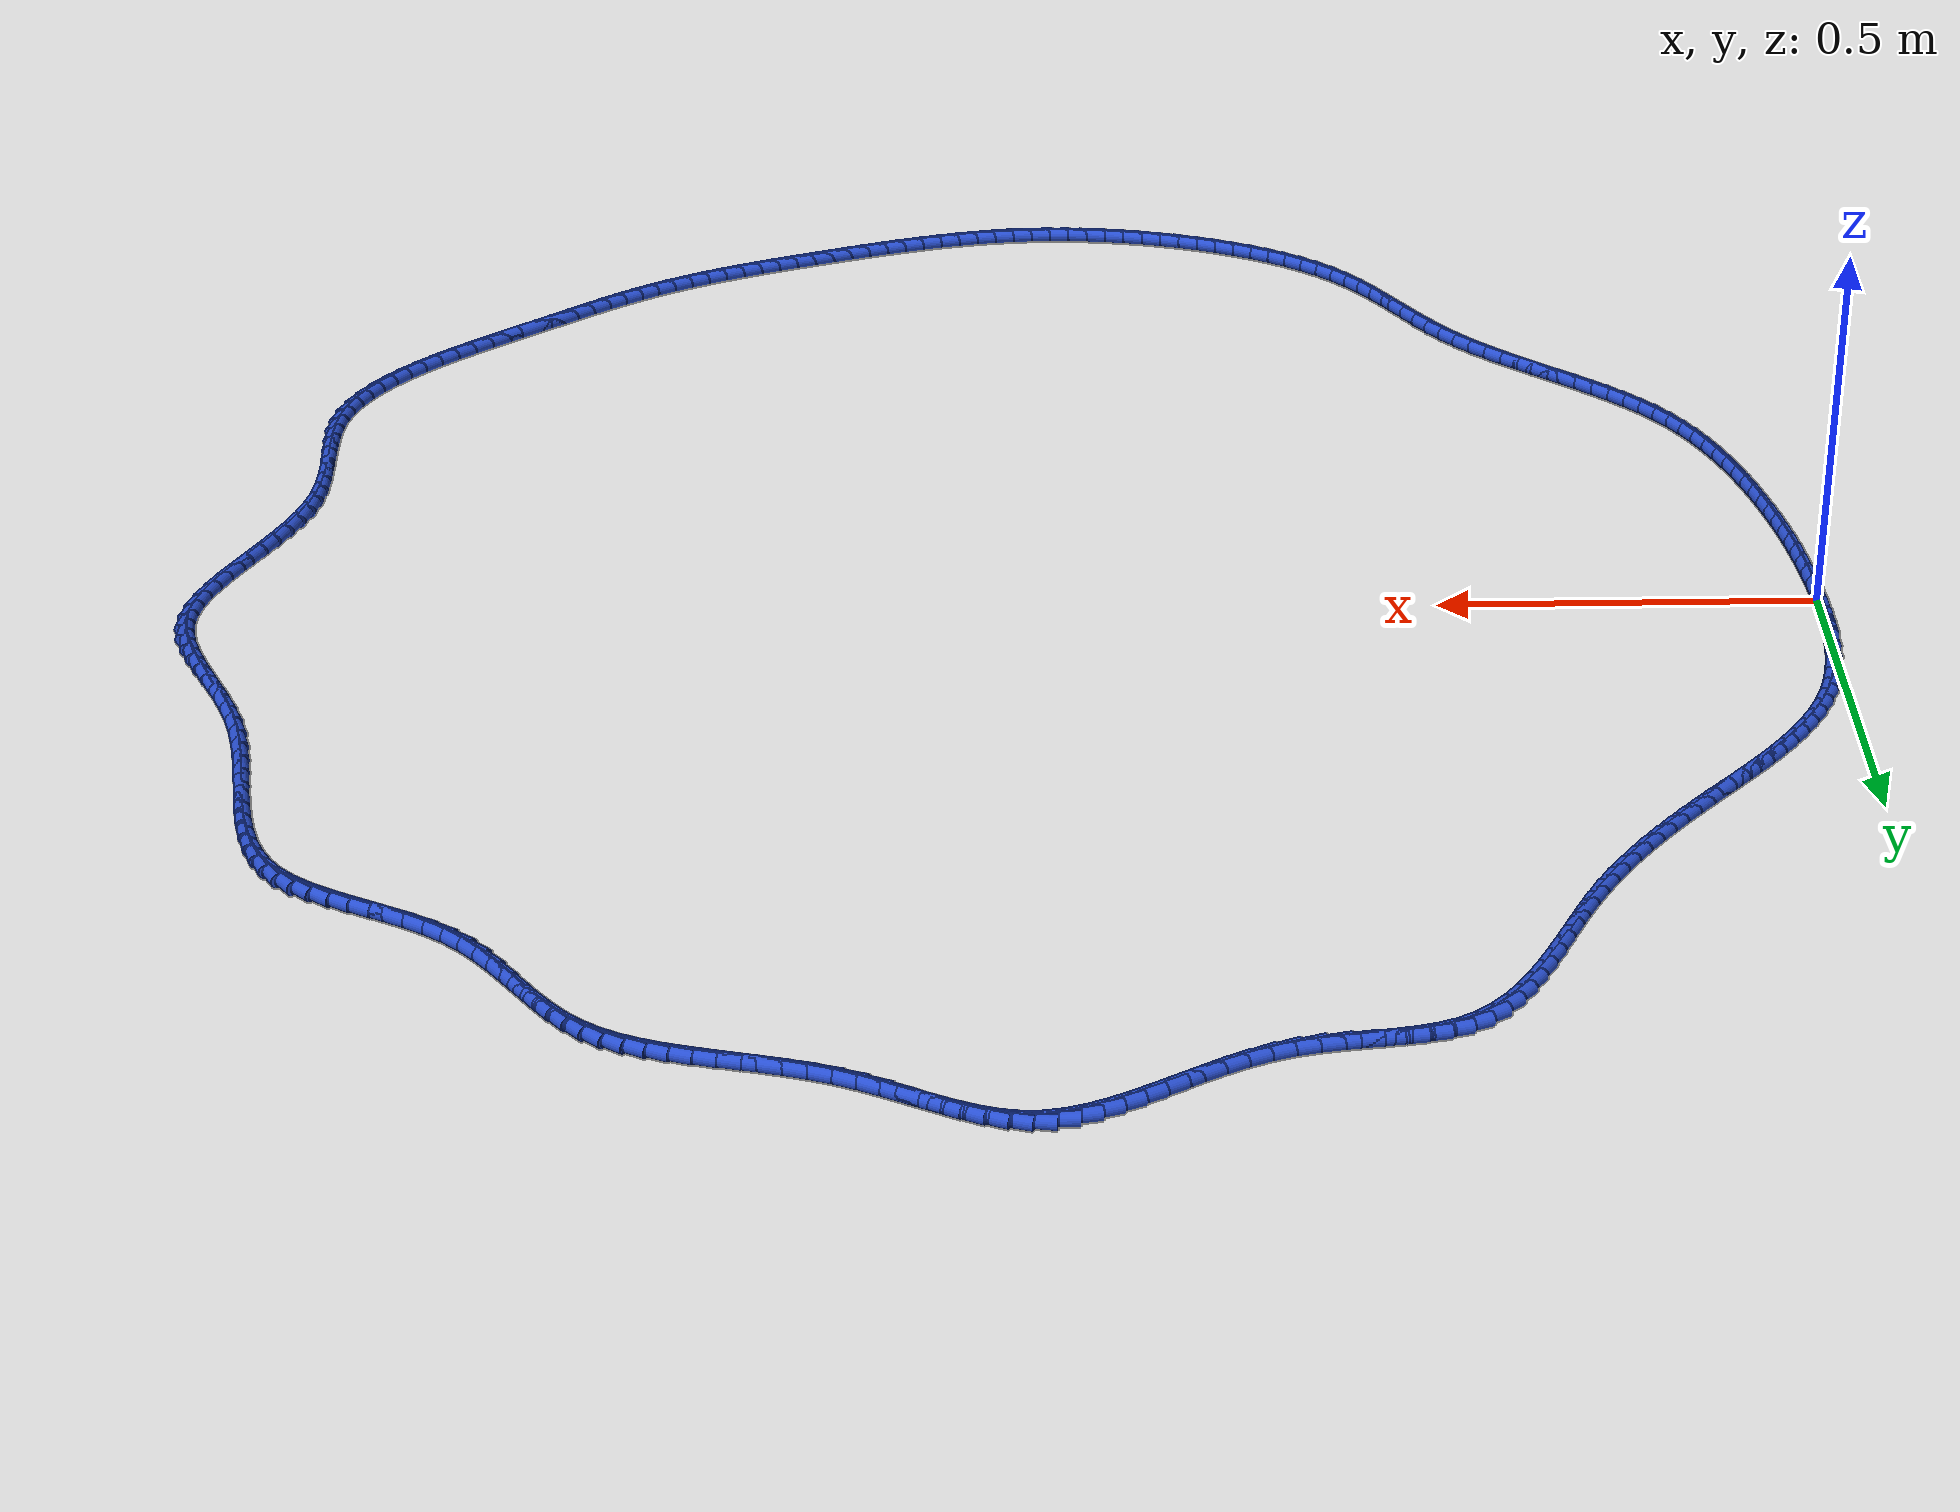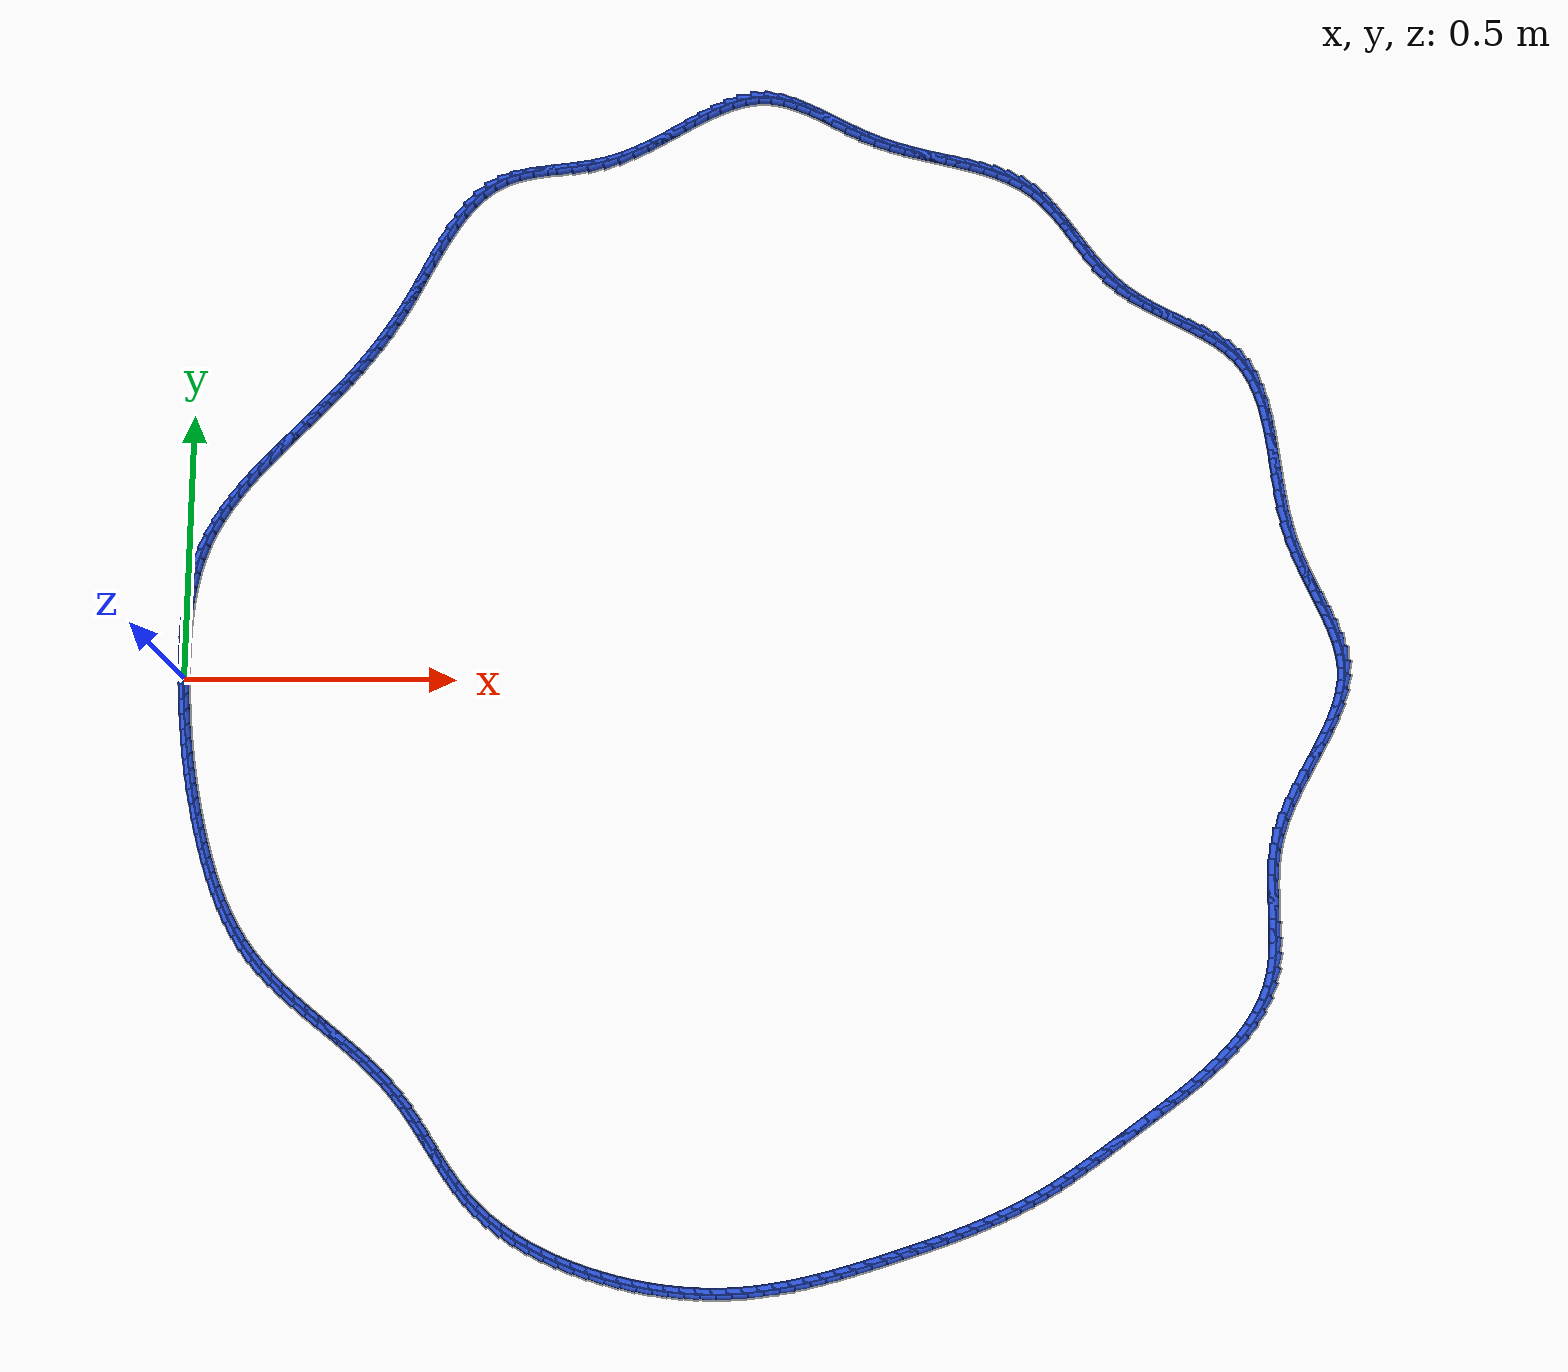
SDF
<sdf version="1.6">
 <world name="default">
  <light name="sun" type="directional">
   <pose>0 0 10 0 -0 0</pose>
   <diffuse>0.8 0.8 0.8 1</diffuse>
   <specular>0.2 0.2 0.2 1</specular>
   <attenuation>
    <range>1000</range>
    <constant>0.9</constant>
    <linear>0.01</linear>
    <quadratic>0.001</quadratic>
   </attenuation>
   <direction>-0.5 0.1 -0.9</direction>
  </light>
  <model name="ground_plane">
   <static>1</static>
   <link name="link">
    <collision name="collision">
     <geometry><plane><normal>0 0 1</normal><size>100 100</size></plane></geometry>
     <surface><friction><ode><mu>100</mu><mu2>50</mu2></ode></friction></surface>
    </collision>
    <visual name="visual">
     <cast_shadows>0</cast_shadows>
     <geometry><plane><normal>0 0 1</normal><size>100 100</size></plane></geometry>
     <material>
      <script><uri>file://media/materials/scripts/gazebo.material</uri><name>Gazebo/WhiteGlow</name></script>
     </material>
    </visual>
   </link>
  </model>
  <gravity>0 0 -9.8</gravity>
  <magnetic_field>6e-06 2.3e-05 -4.2e-05</magnetic_field>
  <atmosphere type="adiabatic"/>
  <physics name="default_physics" default="0" type="ode">
   <max_step_size>0.001</max_step_size>
   <real_time_factor>1</real_time_factor>
   <real_time_update_rate>1000</real_time_update_rate>
  </physics>
  <scene><ambient>0.4 0.4 0.4 1</ambient><background>0.7 0.7 0.7 1</background><shadows>1</shadows></scene>
  <spherical_coordinates>
   <surface_model>EARTH_WGS84</surface_model>
   <latitude_deg>0</latitude_deg>
   <longitude_deg>0</longitude_deg>
   <elevation>0</elevation>
   <heading_deg>0</heading_deg>
  </spherical_coordinates>
  <model name="line">
   <link name="link_0">
    <pose>1.1926223897340549e-17 -3.469446951953614e-17 0.01 0 1.57 -1.5428741788760894</pose>
    <collision name="collision">
     <geometry><cylinder><radius>0.01</radius><length>0.08</length></cylinder></geometry>
    </collision>
    <visual name="visual">
     <material>
      <script><name>Gazebo/Blue</name><uri>file://media/materials/scripts/gazebo.material</uri></script>
     </material>
     <geometry><cylinder><radius>0.01</radius><length>0.08</length></cylinder></geometry>
    </visual>
   </link>
   <link name="link_1">
    <pose>-0.0007957172115728618 0.028490301335886217 0.01 0 1.57 -1.5666635985957107</pose>
    <collision name="collision">
     <geometry><cylinder><radius>0.01</radius><length>0.08</length></cylinder></geometry>
    </collision>
    <visual name="visual">
     <material>
      <script><name>Gazebo/Blue</name><uri>file://media/materials/scripts/gazebo.material</uri></script>
     </material>
     <geometry><cylinder><radius>0.01</radius><length>0.08</length></cylinder></geometry>
    </visual>
   </link>
   <link name="link_2">
    <pose>-0.0009139597867400655 0.05710140187168107 0.01 0 1.57 1.5456756741016464</pose>
    <collision name="collision">
     <geometry><cylinder><radius>0.01</radius><length>0.08</length></cylinder></geometry>
    </collision>
    <visual name="visual">
     <material>
      <script><name>Gazebo/Blue</name><uri>file://media/materials/scripts/gazebo.material</uri></script>
     </material>
     <geometry><cylinder><radius>0.01</radius><length>0.08</length></cylinder></geometry>
    </visual>
   </link>
   <link name="link_3">
    <pose>-0.0001951501861146704 0.08570967101631574 0.01 0 1.57 1.5106396970600608</pose>
    <collision name="collision">
     <geometry><cylinder><radius>0.01</radius><length>0.08</length></cylinder></geometry>
    </collision>
    <visual name="visual">
     <material>
      <script><name>Gazebo/Blue</name><uri>file://media/materials/scripts/gazebo.material</uri></script>
     </material>
     <geometry><cylinder><radius>0.01</radius><length>0.08</length></cylinder></geometry>
    </visual>
   </link>
   <link name="link_4">
    <pose>0.001520289129690251 0.11419147817872134 0.01 0 1.57 1.4694279208050764</pose>
    <collision name="collision">
     <geometry><cylinder><radius>0.01</radius><length>0.08</length></cylinder></geometry>
    </collision>
    <visual name="visual">
     <material>
      <script><name>Gazebo/Blue</name><uri>file://media/materials/scripts/gazebo.material</uri></script>
     </material>
     <geometry><cylinder><radius>0.01</radius><length>0.08</length></cylinder></geometry>
    </visual>
   </link>
   <link name="link_5">
    <pose>0.004391935700061626 0.14242319276782908 0.01 0 1.57 1.4215998209531024</pose>
    <collision name="collision">
     <geometry><cylinder><radius>0.01</radius><length>0.08</length></cylinder></geometry>
    </collision>
    <visual name="visual">
     <material>
      <script><name>Gazebo/Blue</name><uri>file://media/materials/scripts/gazebo.material</uri></script>
     </material>
     <geometry><cylinder><radius>0.01</radius><length>0.08</length></cylinder></geometry>
    </visual>
   </link>
   <link name="link_6">
    <pose>0.008579367064386386 0.1702811841925701 0.01 0 1.57 1.3667092285419515</pose>
    <collision name="collision">
     <geometry><cylinder><radius>0.01</radius><length>0.08</length></cylinder></geometry>
    </collision>
    <visual name="visual">
     <material>
      <script><name>Gazebo/Blue</name><uri>file://media/materials/scripts/gazebo.material</uri></script>
     </material>
     <geometry><cylinder><radius>0.01</radius><length>0.08</length></cylinder></geometry>
    </visual>
   </link>
   <link name="link_7">
    <pose>0.014242160762051453 0.19764182186187568 0.01 0 1.57 1.3043667330624102</pose>
    <collision name="collision">
     <geometry><cylinder><radius>0.01</radius><length>0.08</length></cylinder></geometry>
    </collision>
    <visual name="visual">
     <material>
      <script><name>Gazebo/Blue</name><uri>file://media/materials/scripts/gazebo.material</uri></script>
     </material>
     <geometry><cylinder><radius>0.01</radius><length>0.08</length></cylinder></geometry>
    </visual>
   </link>
   <link name="link_8">
    <pose>0.021539894332443757 0.2243814751846768 0.01 0 1.57 1.2343275733167118</pose>
    <collision name="collision">
     <geometry><cylinder><radius>0.01</radius><length>0.08</length></cylinder></geometry>
    </collision>
    <visual name="visual">
     <material>
      <script><name>Gazebo/Blue</name><uri>file://media/materials/scripts/gazebo.material</uri></script>
     </material>
     <geometry><cylinder><radius>0.01</radius><length>0.08</length></cylinder></geometry>
    </visual>
   </link>
   <link name="link_9">
    <pose>0.03063214531495022 0.2503765135699048 0.01 0 1.57 1.1573862484050812</pose>
    <collision name="collision">
     <geometry><cylinder><radius>0.01</radius><length>0.08</length></cylinder></geometry>
    </collision>
    <visual name="visual">
     <material>
      <script><name>Gazebo/Blue</name><uri>file://media/materials/scripts/gazebo.material</uri></script>
     </material>
     <geometry><cylinder><radius>0.01</radius><length>0.08</length></cylinder></geometry>
    </visual>
   </link>
   <link name="link_10">
    <pose>0.04165959479168924 0.2755136534556845 0.01 0 1.57 1.0830072604641208</pose>
    <collision name="collision">
     <geometry><cylinder><radius>0.01</radius><length>0.08</length></cylinder></geometry>
    </collision>
    <visual name="visual">
     <material>
      <script><name>Gazebo/Blue</name><uri>file://media/materials/scripts/gazebo.material</uri></script>
     </material>
     <geometry><cylinder><radius>0.01</radius><length>0.08</length></cylinder></geometry>
    </visual>
   </link>
   <link name="link_11">
    <pose>0.05454437246575533 0.29979928225692576 0.01 0 1.57 1.0175543864455008</pose>
    <collision name="collision">
     <geometry><cylinder><radius>0.01</radius><length>0.08</length></cylinder></geometry>
    </collision>
    <visual name="visual">
     <material>
      <script><name>Gazebo/Blue</name><uri>file://media/materials/scripts/gazebo.material</uri></script>
     </material>
     <geometry><cylinder><radius>0.01</radius><length>0.08</length></cylinder></geometry>
    </visual>
   </link>
   <link name="link_12">
    <pose>0.06906813712449951 0.3233167042754136 0.01 0 1.57 0.9612929282947866</pose>
    <collision name="collision">
     <geometry><cylinder><radius>0.01</radius><length>0.08</length></cylinder></geometry>
    </collision>
    <visual name="visual">
     <material>
      <script><name>Gazebo/Blue</name><uri>file://media/materials/scripts/gazebo.material</uri></script>
     </material>
     <geometry><cylinder><radius>0.01</radius><length>0.08</length></cylinder></geometry>
    </visual>
   </link>
   <link name="link_13">
    <pose>0.08501023006902264 0.34615049278613536 0.01 0 1.57 0.914080761599901</pose>
    <collision name="collision">
     <geometry><cylinder><radius>0.01</radius><length>0.08</length></cylinder></geometry>
    </collision>
    <visual name="visual">
     <material>
      <script><name>Gazebo/Blue</name><uri>file://media/materials/scripts/gazebo.material</uri></script>
     </material>
     <geometry><cylinder><radius>0.01</radius><length>0.08</length></cylinder></geometry>
    </visual>
   </link>
   <link name="link_14">
    <pose>0.10214999260042561 0.3683852210640782 0.01 0 1.57 0.8756079305600076</pose>
    <collision name="collision">
     <geometry><cylinder><radius>0.01</radius><length>0.08</length></cylinder></geometry>
    </collision>
    <visual name="visual">
     <material>
      <script><name>Gazebo/Blue</name><uri>file://media/materials/scripts/gazebo.material</uri></script>
     </material>
     <geometry><cylinder><radius>0.01</radius><length>0.08</length></cylinder></geometry>
    </visual>
   </link>
   <link name="link_15">
    <pose>0.12026676601980935 0.3901054623842294 0.01 0 1.57 0.845509774532502</pose>
    <collision name="collision">
     <geometry><cylinder><radius>0.01</radius><length>0.08</length></cylinder></geometry>
    </collision>
    <visual name="visual">
     <material>
      <script><name>Gazebo/Blue</name><uri>file://media/materials/scripts/gazebo.material</uri></script>
     </material>
     <geometry><cylinder><radius>0.01</radius><length>0.08</length></cylinder></geometry>
    </visual>
   </link>
   <link name="link_16">
    <pose>0.1391398916282747 0.4113957900215761 0.01 0 1.57 0.8234472813712401</pose>
    <collision name="collision">
     <geometry><cylinder><radius>0.01</radius><length>0.08</length></cylinder></geometry>
    </collision>
    <visual name="visual">
     <material>
      <script><name>Gazebo/Blue</name><uri>file://media/materials/scripts/gazebo.material</uri></script>
     </material>
     <geometry><cylinder><radius>0.01</radius><length>0.08</length></cylinder></geometry>
    </visual>
   </link>
   <link name="link_17">
    <pose>0.15854871072692264 0.43234077725110565 0.01 0 1.57 0.8091603809582558</pose>
    <collision name="collision">
     <geometry><cylinder><radius>0.01</radius><length>0.08</length></cylinder></geometry>
    </collision>
    <visual name="visual">
     <material>
      <script><name>Gazebo/Blue</name><uri>file://media/materials/scripts/gazebo.material</uri></script>
     </material>
     <geometry><cylinder><radius>0.01</radius><length>0.08</length></cylinder></geometry>
    </visual>
   </link>
   <link name="link_18">
    <pose>0.17827256461685392 0.453024997347805 0.01 0 1.57 0.8025018833100955</pose>
    <collision name="collision">
     <geometry><cylinder><radius>0.01</radius><length>0.08</length></cylinder></geometry>
    </collision>
    <visual name="visual">
     <material>
      <script><name>Gazebo/Blue</name><uri>file://media/materials/scripts/gazebo.material</uri></script>
     </material>
     <geometry><cylinder><radius>0.01</radius><length>0.08</length></cylinder></geometry>
    </visual>
   </link>
   <link name="link_19">
    <pose>0.19809079459916956 0.47353302358666155 0.01 0 1.57 0.8034587282132746</pose>
    <collision name="collision">
     <geometry><cylinder><radius>0.01</radius><length>0.08</length></cylinder></geometry>
    </collision>
    <visual name="visual">
     <material>
      <script><name>Gazebo/Blue</name><uri>file://media/materials/scripts/gazebo.material</uri></script>
     </material>
     <geometry><cylinder><radius>0.01</radius><length>0.08</length></cylinder></geometry>
    </visual>
   </link>
   <link name="link_20">
    <pose>0.21778274197497038 0.49394942924266244 0.01 0 1.57 0.8120332511163459</pose>
    <collision name="collision">
     <geometry><cylinder><radius>0.01</radius><length>0.08</length></cylinder></geometry>
    </collision>
    <visual name="visual">
     <material>
      <script><name>Gazebo/Blue</name><uri>file://media/materials/scripts/gazebo.material</uri></script>
     </material>
     <geometry><cylinder><radius>0.01</radius><length>0.08</length></cylinder></geometry>
    </visual>
   </link>
   <link name="link_21">
    <pose>0.2371333449957688 0.5143593066522519 0.01 0 1.57 0.8259299389931999</pose>
    <collision name="collision">
     <geometry><cylinder><radius>0.01</radius><length>0.08</length></cylinder></geometry>
    </collision>
    <visual name="visual">
     <material>
      <script><name>Gazebo/Blue</name><uri>file://media/materials/scripts/gazebo.material</uri></script>
     </material>
     <geometry><cylinder><radius>0.01</radius><length>0.08</length></cylinder></geometry>
    </visual>
   </link>
   <link name="link_22">
    <pose>0.2560338677767003 0.5348576088177052 0.01 0 1.57 0.8429312597894141</pose>
    <collision name="collision">
     <geometry><cylinder><radius>0.01</radius><length>0.08</length></cylinder></geometry>
    </collision>
    <visual name="visual">
     <material>
      <script><name>Gazebo/Blue</name><uri>file://media/materials/scripts/gazebo.material</uri></script>
     </material>
     <geometry><cylinder><radius>0.01</radius><length>0.08</length></cylinder></geometry>
    </visual>
   </link>
   <link name="link_23">
    <pose>0.2744707679221668 0.5555481169901817 0.01 0 1.57 0.8628735238864457</pose>
    <collision name="collision">
     <geometry><cylinder><radius>0.01</radius><length>0.08</length></cylinder></geometry>
    </collision>
    <visual name="visual">
     <material>
      <script><name>Gazebo/Blue</name><uri>file://media/materials/scripts/gazebo.material</uri></script>
     </material>
     <geometry><cylinder><radius>0.01</radius><length>0.08</length></cylinder></geometry>
    </visual>
   </link>
   <link name="link_24">
    <pose>0.2924338649714685 0.5765349242068498 0.01 0 1.57 0.885613328818217</pose>
    <collision name="collision">
     <geometry><cylinder><radius>0.01</radius><length>0.08</length></cylinder></geometry>
    </collision>
    <visual name="visual">
     <material>
      <script><name>Gazebo/Blue</name><uri>file://media/materials/scripts/gazebo.material</uri></script>
     </material>
     <geometry><cylinder><radius>0.01</radius><length>0.08</length></cylinder></geometry>
    </visual>
   </link>
   <link name="link_25">
    <pose>0.30991297846390525 0.5979221235048774 0.01 0 1.57 0.9109472757408055</pose>
    <collision name="collision">
     <geometry><cylinder><radius>0.01</radius><length>0.08</length></cylinder></geometry>
    </collision>
    <visual name="visual">
     <material>
      <script><name>Gazebo/Blue</name><uri>file://media/materials/scripts/gazebo.material</uri></script>
     </material>
     <geometry><cylinder><radius>0.01</radius><length>0.08</length></cylinder></geometry>
    </visual>
   </link>
   <link name="link_26">
    <pose>0.3268979279387771 0.619813807921432 0.01 0 1.57 0.9386138345866768</pose>
    <collision name="collision">
     <geometry><cylinder><radius>0.01</radius><length>0.08</length></cylinder></geometry>
    </collision>
    <visual name="visual">
     <material>
      <script><name>Gazebo/Blue</name><uri>file://media/materials/scripts/gazebo.material</uri></script>
     </material>
     <geometry><cylinder><radius>0.01</radius><length>0.08</length></cylinder></geometry>
    </visual>
   </link>
   <link name="link_27">
    <pose>0.3433785329353842 0.642314070493682 0.01 0 1.57 0.9682987386237965</pose>
    <collision name="collision">
     <geometry><cylinder><radius>0.01</radius><length>0.08</length></cylinder></geometry>
    </collision>
    <visual name="visual">
     <material>
      <script><name>Gazebo/Blue</name><uri>file://media/materials/scripts/gazebo.material</uri></script>
     </material>
     <geometry><cylinder><radius>0.01</radius><length>0.08</length></cylinder></geometry>
    </visual>
   </link>
   <link name="link_28">
    <pose>0.35934461299302645 0.6655270042587953 0.01 0 1.57 0.9996440361477207</pose>
    <collision name="collision">
     <geometry><cylinder><radius>0.01</radius><length>0.08</length></cylinder></geometry>
    </collision>
    <visual name="visual">
     <material>
      <script><name>Gazebo/Blue</name><uri>file://media/materials/scripts/gazebo.material</uri></script>
     </material>
     <geometry><cylinder><radius>0.01</radius><length>0.08</length></cylinder></geometry>
    </visual>
   </link>
   <link name="link_29">
    <pose>0.37478598765100407 0.68955670225394 0.01 0 1.57 1.032260447206589</pose>
    <collision name="collision">
     <geometry><cylinder><radius>0.01</radius><length>0.08</length></cylinder></geometry>
    </collision>
    <visual name="visual">
     <material>
      <script><name>Gazebo/Blue</name><uri>file://media/materials/scripts/gazebo.material</uri></script>
     </material>
     <geometry><cylinder><radius>0.01</radius><length>0.08</length></cylinder></geometry>
    </visual>
   </link>
   <link name="link_30">
    <pose>0.3896924764486169 0.7145072575162833 0.01 0 1.57 1.0638584284777615</pose>
    <collision name="collision">
     <geometry><cylinder><radius>0.01</radius><length>0.08</length></cylinder></geometry>
    </collision>
    <visual name="visual">
     <material>
      <script><name>Gazebo/Blue</name><uri>file://media/materials/scripts/gazebo.material</uri></script>
     </material>
     <geometry><cylinder><radius>0.01</radius><length>0.08</length></cylinder></geometry>
    </visual>
   </link>
   <link name="link_31">
    <pose>0.4040833503678762 0.740420633154815 0.01 0 1.57 1.083862108969824</pose>
    <collision name="collision">
     <geometry><cylinder><radius>0.01</radius><length>0.08</length></cylinder></geometry>
    </collision>
    <visual name="visual">
     <material>
      <script><name>Gazebo/Blue</name><uri>file://media/materials/scripts/gazebo.material</uri></script>
     </material>
     <geometry><cylinder><radius>0.01</radius><length>0.08</length></cylinder></geometry>
    </visual>
   </link>
   <link name="link_32">
    <pose>0.418146741156637 0.7669825683964935 0.01 0 1.57 1.0893978605649979</pose>
    <collision name="collision">
     <geometry><cylinder><radius>0.01</radius><length>0.08</length></cylinder></geometry>
    </collision>
    <visual name="visual">
     <material>
      <script><name>Gazebo/Blue</name><uri>file://media/materials/scripts/gazebo.material</uri></script>
     </material>
     <geometry><cylinder><radius>0.01</radius><length>0.08</length></cylinder></geometry>
    </visual>
   </link>
   <link name="link_33">
    <pose>0.43213085361098635 0.7937520740696465 0.01 0 1.57 1.0808209969836258</pose>
    <collision name="collision">
     <geometry><cylinder><radius>0.01</radius><length>0.08</length></cylinder></geometry>
    </collision>
    <visual name="visual">
     <material>
      <script><name>Gazebo/Blue</name><uri>file://media/materials/scripts/gazebo.material</uri></script>
     </material>
     <geometry><cylinder><radius>0.01</radius><length>0.08</length></cylinder></geometry>
    </visual>
   </link>
   <link name="link_34">
    <pose>0.4462839651914178 0.8202880077118311 0.01 0 1.57 1.0577182459632406</pose>
    <collision name="collision">
     <geometry><cylinder><radius>0.01</radius><length>0.08</length></cylinder></geometry>
    </collision>
    <visual name="visual">
     <material>
      <script><name>Gazebo/Blue</name><uri>file://media/materials/scripts/gazebo.material</uri></script>
     </material>
     <geometry><cylinder><radius>0.01</radius><length>0.08</length></cylinder></geometry>
    </visual>
   </link>
   <link name="link_35">
    <pose>0.460854353358425 0.8461492268606053 0.01 0 1.57 1.0189060949640123</pose>
    <collision name="collision">
     <geometry><cylinder><radius>0.01</radius><length>0.08</length></cylinder></geometry>
    </collision>
    <visual name="visual">
     <material>
      <script><name>Gazebo/Blue</name><uri>file://media/materials/scripts/gazebo.material</uri></script>
     </material>
     <geometry><cylinder><radius>0.01</radius><length>0.08</length></cylinder></geometry>
    </visual>
   </link>
   <link name="link_36">
    <pose>0.4760902955725016 0.8708945890535259 0.01 0 1.57 0.9624499634647101</pose>
    <collision name="collision">
     <geometry><cylinder><radius>0.01</radius><length>0.08</length></cylinder></geometry>
    </collision>
    <visual name="visual">
     <material>
      <script><name>Gazebo/Blue</name><uri>file://media/materials/scripts/gazebo.material</uri></script>
     </material>
     <geometry><cylinder><radius>0.01</radius><length>0.08</length></cylinder></geometry>
    </visual>
   </link>
   <link name="link_37">
    <pose>0.4922400692941411 0.8940829518281505 0.01 0 1.57 0.8857900837261249</pose>
    <collision name="collision">
     <geometry><cylinder><radius>0.01</radius><length>0.08</length></cylinder></geometry>
    </collision>
    <visual name="visual">
     <material>
      <script><name>Gazebo/Blue</name><uri>file://media/materials/scripts/gazebo.material</uri></script>
     </material>
     <geometry><cylinder><radius>0.01</radius><length>0.08</length></cylinder></geometry>
    </visual>
   </link>
   <link name="link_38">
    <pose>0.5095519519838368 0.9152731727220363 0.01 0 1.57 0.7861631747263254</pose>
    <collision name="collision">
     <geometry><cylinder><radius>0.01</radius><length>0.08</length></cylinder></geometry>
    </collision>
    <visual name="visual">
     <material>
      <script><name>Gazebo/Blue</name><uri>file://media/materials/scripts/gazebo.material</uri></script>
     </material>
     <geometry><cylinder><radius>0.01</radius><length>0.08</length></cylinder></geometry>
    </visual>
   </link>
   <link name="link_39">
    <pose>0.5282742211020827 0.9340241092727407 0.01 0 1.57 0.6616137770099053</pose>
    <collision name="collision">
     <geometry><cylinder><radius>0.01</radius><length>0.08</length></cylinder></geometry>
    </collision>
    <visual name="visual">
     <material>
      <script><name>Gazebo/Blue</name><uri>file://media/materials/scripts/gazebo.material</uri></script>
     </material>
     <geometry><cylinder><radius>0.01</radius><length>0.08</length></cylinder></geometry>
    </visual>
   </link>
   <link name="link_40">
    <pose>0.5486551541093719 0.949894619017821 0.01 0 1.57 0.5128230388341847</pose>
    <collision name="collision">
     <geometry><cylinder><radius>0.01</radius><length>0.08</length></cylinder></geometry>
    </collision>
    <visual name="visual">
     <material>
      <script><name>Gazebo/Blue</name><uri>file://media/materials/scripts/gazebo.material</uri></script>
     </material>
     <geometry><cylinder><radius>0.01</radius><length>0.08</length></cylinder></geometry>
    </visual>
   </link>
   <link name="link_41">
    <pose>0.5709427631343595 0.9624441231962502 0.01 0 1.57 0.3589645401083616</pose>
    <collision name="collision">
     <geometry><cylinder><radius>0.01</radius><length>0.08</length></cylinder></geometry>
    </collision>
    <visual name="visual">
     <material>
      <script><name>Gazebo/Blue</name><uri>file://media/materials/scripts/gazebo.material</uri></script>
     </material>
     <geometry><cylinder><radius>0.01</radius><length>0.08</length></cylinder></geometry>
    </visual>
   </link>
   <link name="link_42">
    <pose>0.5952317053174303 0.9715578479868802 0.01 0 1.57 0.24285056643595912</pose>
    <collision name="collision">
     <geometry><cylinder><radius>0.01</radius><length>0.08</length></cylinder></geometry>
    </collision>
    <visual name="visual">
     <material>
      <script><name>Gazebo/Blue</name><uri>file://media/materials/scripts/gazebo.material</uri></script>
     </material>
     <geometry><cylinder><radius>0.01</radius><length>0.08</length></cylinder></geometry>
    </visual>
   </link>
   <link name="link_43">
    <pose>0.6212062965085824 0.9779927957067559 0.01 0 1.57 0.16911727179858327</pose>
    <collision name="collision">
     <geometry><cylinder><radius>0.01</radius><length>0.08</length></cylinder></geometry>
    </collision>
    <visual name="visual">
     <material>
      <script><name>Gazebo/Blue</name><uri>file://media/materials/scripts/gazebo.material</uri></script>
     </material>
     <geometry><cylinder><radius>0.01</radius><length>0.08</length></cylinder></geometry>
    </visual>
   </link>
   <link name="link_44">
    <pose>0.6484829469061665 0.9826502352338055 0.01 0 1.57 0.1333129068355688</pose>
    <collision name="collision">
     <geometry><cylinder><radius>0.01</radius><length>0.08</length></cylinder></geometry>
    </collision>
    <visual name="visual">
     <material>
      <script><name>Gazebo/Blue</name><uri>file://media/materials/scripts/gazebo.material</uri></script>
     </material>
     <geometry><cylinder><radius>0.01</radius><length>0.08</length></cylinder></geometry>
    </visual>
   </link>
   <link name="link_45">
    <pose>0.6766780667085345 0.9864314354459578 0.01 0 1.57 0.1317157286446269</pose>
    <collision name="collision">
     <geometry><cylinder><radius>0.01</radius><length>0.08</length></cylinder></geometry>
    </collision>
    <visual name="visual">
     <material>
      <script><name>Gazebo/Blue</name><uri>file://media/materials/scripts/gazebo.material</uri></script>
     </material>
     <geometry><cylinder><radius>0.01</radius><length>0.08</length></cylinder></geometry>
    </visual>
   </link>
   <link name="link_46">
    <pose>0.7054080661140368 0.9902376652211419 0.01 0 1.57 0.16241798433288324</pose>
    <collision name="collision">
     <geometry><cylinder><radius>0.01</radius><length>0.08</length></cylinder></geometry>
    </collision>
    <visual name="visual">
     <material>
      <script><name>Gazebo/Blue</name><uri>file://media/materials/scripts/gazebo.material</uri></script>
     </material>
     <geometry><cylinder><radius>0.01</radius><length>0.08</length></cylinder></geometry>
    </visual>
   </link>
   <link name="link_47">
    <pose>0.7342893553210256 0.9949701934372872 0.01 0 1.57 0.22510107729409648</pose>
    <collision name="collision">
     <geometry><cylinder><radius>0.01</radius><length>0.08</length></cylinder></geometry>
    </collision>
    <visual name="visual">
     <material>
      <script><name>Gazebo/Blue</name><uri>file://media/materials/scripts/gazebo.material</uri></script>
     </material>
     <geometry><cylinder><radius>0.01</radius><length>0.08</length></cylinder></geometry>
    </visual>
   </link>
   <link name="link_48">
    <pose>0.7629383445278517 1.001530288972322 0.01 0 1.57 0.31553224103313365</pose>
    <collision name="collision">
     <geometry><cylinder><radius>0.01</radius><length>0.08</length></cylinder></geometry>
    </collision>
    <visual name="visual">
     <material>
      <script><name>Gazebo/Blue</name><uri>file://media/materials/scripts/gazebo.material</uri></script>
     </material>
     <geometry><cylinder><radius>0.01</radius><length>0.08</length></cylinder></geometry>
    </visual>
   </link>
   <link name="link_49">
    <pose>0.7910083011799036 1.010693397880971 0.01 0 1.57 0.39926055064568844</pose>
    <collision name="collision">
     <geometry><cylinder><radius>0.01</radius><length>0.08</length></cylinder></geometry>
    </collision>
    <visual name="visual">
     <material>
      <script><name>Gazebo/Blue</name><uri>file://media/materials/scripts/gazebo.material</uri></script>
     </material>
     <geometry><cylinder><radius>0.01</radius><length>0.08</length></cylinder></geometry>
    </visual>
   </link>
   <link name="link_50">
    <pose>0.8184363620899946 1.0222658964121054 0.01 0 1.57 0.46097882196133094</pose>
    <collision name="collision">
     <geometry><cylinder><radius>0.01</radius><length>0.08</length></cylinder></geometry>
    </collision>
    <visual name="visual">
     <material>
      <script><name>Gazebo/Blue</name><uri>file://media/materials/scripts/gazebo.material</uri></script>
     </material>
     <geometry><cylinder><radius>0.01</radius><length>0.08</length></cylinder></geometry>
    </visual>
   </link>
   <link name="link_51">
    <pose>0.8452915267695528 1.035604009532319 0.01 0 1.57 0.5017899645064001</pose>
    <collision name="collision">
     <geometry><cylinder><radius>0.01</radius><length>0.08</length></cylinder></geometry>
    </collision>
    <visual name="visual">
     <material>
      <script><name>Gazebo/Blue</name><uri>file://media/materials/scripts/gazebo.material</uri></script>
     </material>
     <geometry><cylinder><radius>0.01</radius><length>0.08</length></cylinder></geometry>
    </visual>
   </link>
   <link name="link_52">
    <pose>0.8716435226847515 1.050061477125119 0.01 0 1.57 0.5226281974443435</pose>
    <collision name="collision">
     <geometry><cylinder><radius>0.01</radius><length>0.08</length></cylinder></geometry>
    </collision>
    <visual name="visual">
     <material>
      <script><name>Gazebo/Blue</name><uri>file://media/materials/scripts/gazebo.material</uri></script>
     </material>
     <geometry><cylinder><radius>0.01</radius><length>0.08</length></cylinder></geometry>
    </visual>
   </link>
   <link name="link_53">
    <pose>0.8975620773017633 1.0649920390740137 0.01 0 1.57 0.5236956788854874</pose>
    <collision name="collision">
     <geometry><cylinder><radius>0.01</radius><length>0.08</length></cylinder></geometry>
    </collision>
    <visual name="visual">
     <material>
      <script><name>Gazebo/Blue</name><uri>file://media/materials/scripts/gazebo.material</uri></script>
     </material>
     <geometry><cylinder><radius>0.01</radius><length>0.08</length></cylinder></geometry>
    </visual>
   </link>
   <link name="link_54">
    <pose>0.9231169180867622 1.0797494352625119 0.01 0 1.57 0.5041947069022281</pose>
    <collision name="collision">
     <geometry><cylinder><radius>0.01</radius><length>0.08</length></cylinder></geometry>
    </collision>
    <visual name="visual">
     <material>
      <script><name>Gazebo/Blue</name><uri>file://media/materials/scripts/gazebo.material</uri></script>
     </material>
     <geometry><cylinder><radius>0.01</radius><length>0.08</length></cylinder></geometry>
    </visual>
   </link>
   <link name="link_55">
    <pose>0.94837777250592 1.093687405574121 0.01 0 1.57 0.46217625050367384</pose>
    <collision name="collision">
     <geometry><cylinder><radius>0.01</radius><length>0.08</length></cylinder></geometry>
    </collision>
    <visual name="visual">
     <material>
      <script><name>Gazebo/Blue</name><uri>file://media/materials/scripts/gazebo.material</uri></script>
     </material>
     <geometry><cylinder><radius>0.01</radius><length>0.08</length></cylinder></geometry>
    </visual>
   </link>
   <link name="link_56">
    <pose>0.9734143680254107 1.1061596898923496 0.01 0 1.57 0.3945449288853501</pose>
    <collision name="collision">
     <geometry><cylinder><radius>0.01</radius><length>0.08</length></cylinder></geometry>
    </collision>
    <visual name="visual">
     <material>
      <script><name>Gazebo/Blue</name><uri>file://media/materials/scripts/gazebo.material</uri></script>
     </material>
     <geometry><cylinder><radius>0.01</radius><length>0.08</length></cylinder></geometry>
    </visual>
   </link>
   <link name="link_57">
    <pose>0.9982964321114068 1.1165200281007057 0.01 0 1.57 0.29747469028885454</pose>
    <collision name="collision">
     <geometry><cylinder><radius>0.01</radius><length>0.08</length></cylinder></geometry>
    </collision>
    <visual name="visual">
     <material>
      <script><name>Gazebo/Blue</name><uri>file://media/materials/scripts/gazebo.material</uri></script>
     </material>
     <geometry><cylinder><radius>0.01</radius><length>0.08</length></cylinder></geometry>
    </visual>
   </link>
   <link name="link_58">
    <pose>1.0230936922300813 1.1241221600826972 0.01 0 1.57 0.16778983937189812</pose>
    <collision name="collision">
     <geometry><cylinder><radius>0.01</radius><length>0.08</length></cylinder></geometry>
    </collision>
    <visual name="visual">
     <material>
      <script><name>Gazebo/Blue</name><uri>file://media/materials/scripts/gazebo.material</uri></script>
     </material>
     <geometry><cylinder><radius>0.01</radius><length>0.08</length></cylinder></geometry>
    </visual>
   </link>
   <link name="link_59">
    <pose>1.0478758758476074 1.1283198257218325 0.01 0 1.57 0.00601099778260239</pose>
    <collision name="collision">
     <geometry><cylinder><radius>0.01</radius><length>0.08</length></cylinder></geometry>
    </collision>
    <visual name="visual">
     <material>
      <script><name>Gazebo/Blue</name><uri>file://media/materials/scripts/gazebo.material</uri></script>
     </material>
     <geometry><cylinder><radius>0.01</radius><length>0.08</length></cylinder></geometry>
    </visual>
   </link>
   <link name="link_60">
    <pose>1.0727127009879251 1.1284691216208067 0.01 0 1.57 -0.16331660266532677</pose>
    <collision name="collision">
     <geometry><cylinder><radius>0.01</radius><length>0.08</length></cylinder></geometry>
    </collision>
    <visual name="visual">
     <material>
      <script><name>Gazebo/Blue</name><uri>file://media/materials/scripts/gazebo.material</uri></script>
     </material>
     <geometry><cylinder><radius>0.01</radius><length>0.08</length></cylinder></geometry>
    </visual>
   </link>
   <link name="link_61">
    <pose>1.0976721626707933 1.124356194857279 0.01 0 1.57 -0.2957451794228205</pose>
    <collision name="collision">
     <geometry><cylinder><radius>0.01</radius><length>0.08</length></cylinder></geometry>
    </collision>
    <visual name="visual">
     <material>
      <script><name>Gazebo/Blue</name><uri>file://media/materials/scripts/gazebo.material</uri></script>
     </material>
     <geometry><cylinder><radius>0.01</radius><length>0.08</length></cylinder></geometry>
    </visual>
   </link>
   <link name="link_62">
    <pose>1.1228185402960609 1.1166945867234979 0.01 0 1.57 -0.38785912382981985</pose>
    <collision name="collision">
     <geometry><cylinder><radius>0.01</radius><length>0.08</length></cylinder></geometry>
    </collision>
    <visual name="visual">
     <material>
      <script><name>Gazebo/Blue</name><uri>file://media/materials/scripts/gazebo.material</uri></script>
     </material>
     <geometry><cylinder><radius>0.01</radius><length>0.08</length></cylinder></geometry>
    </visual>
   </link>
   <link name="link_63">
    <pose>1.1482156298654553 1.1063184914934814 0.01 0 1.57 -0.44482399619984925</pose>
    <collision name="collision">
     <geometry><cylinder><radius>0.01</radius><length>0.08</length></cylinder></geometry>
    </collision>
    <visual name="visual">
     <material>
      <script><name>Gazebo/Blue</name><uri>file://media/materials/scripts/gazebo.material</uri></script>
     </material>
     <geometry><cylinder><radius>0.01</radius><length>0.08</length></cylinder></geometry>
    </visual>
   </link>
   <link name="link_64">
    <pose>1.173927227380702 1.0940621034412468 0.01 0 1.57 -0.47151326427162166</pose>
    <collision name="collision">
     <geometry><cylinder><radius>0.01</radius><length>0.08</length></cylinder></geometry>
    </collision>
    <visual name="visual">
     <material>
      <script><name>Gazebo/Blue</name><uri>file://media/materials/scripts/gazebo.material</uri></script>
     </material>
     <geometry><cylinder><radius>0.01</radius><length>0.08</length></cylinder></geometry>
    </visual>
   </link>
   <link name="link_65">
    <pose>1.200017128843528 1.0807596168408118 0.01 0 1.57 -0.4711090554304261</pose>
    <collision name="collision">
     <geometry><cylinder><radius>0.01</radius><length>0.08</length></cylinder></geometry>
    </collision>
    <visual name="visual">
     <material>
      <script><name>Gazebo/Blue</name><uri>file://media/materials/scripts/gazebo.material</uri></script>
     </material>
     <geometry><cylinder><radius>0.01</radius><length>0.08</length></cylinder></geometry>
    </visual>
   </link>
   <link name="link_66">
    <pose>1.2265491302556608 1.067245225966194 0.01 0 1.57 -0.44492895027313606</pose>
    <collision name="collision">
     <geometry><cylinder><radius>0.01</radius><length>0.08</length></cylinder></geometry>
    </collision>
    <visual name="visual">
     <material>
      <script><name>Gazebo/Blue</name><uri>file://media/materials/scripts/gazebo.material</uri></script>
     </material>
     <geometry><cylinder><radius>0.01</radius><length>0.08</length></cylinder></geometry>
    </visual>
   </link>
   <link name="link_67">
    <pose>1.2535870276188255 1.0543531250914107 0.01 0 1.57 -0.39299823563864233</pose>
    <collision name="collision">
     <geometry><cylinder><radius>0.01</radius><length>0.08</length></cylinder></geometry>
    </collision>
    <visual name="visual">
     <material>
      <script><name>Gazebo/Blue</name><uri>file://media/materials/scripts/gazebo.material</uri></script>
     </material>
     <geometry><cylinder><radius>0.01</radius><length>0.08</length></cylinder></geometry>
    </visual>
   </link>
   <link name="link_68">
    <pose>1.2811926713797106 1.0429088166045448 0.01 0 1.57 -0.33049163172046775</pose>
    <collision name="collision">
     <geometry><cylinder><radius>0.01</radius><length>0.08</length></cylinder></geometry>
    </collision>
    <visual name="visual">
     <material>
      <script><name>Gazebo/Blue</name><uri>file://media/materials/scripts/gazebo.material</uri></script>
     </material>
     <geometry><cylinder><radius>0.01</radius><length>0.08</length></cylinder></geometry>
    </visual>
   </link>
   <link name="link_69">
    <pose>1.3093206972702804 1.033258814608885 0.01 0 1.57 -0.2815875881725501</pose>
    <collision name="collision">
     <geometry><cylinder><radius>0.01</radius><length>0.08</length></cylinder></geometry>
    </collision>
    <visual name="visual">
     <material>
      <script><name>Gazebo/Blue</name><uri>file://media/materials/scripts/gazebo.material</uri></script>
     </material>
     <geometry><cylinder><radius>0.01</radius><length>0.08</length></cylinder></geometry>
    </visual>
   </link>
   <link name="link_70">
    <pose>1.3377648119008756 1.0250306725301932 0.01 0 1.57 -0.24836396946843792</pose>
    <collision name="collision">
     <geometry><cylinder><radius>0.01</radius><length>0.08</length></cylinder></geometry>
    </collision>
    <visual name="visual">
     <material>
      <script><name>Gazebo/Blue</name><uri>file://media/materials/scripts/gazebo.material</uri></script>
     </material>
     <geometry><cylinder><radius>0.01</radius><length>0.08</length></cylinder></geometry>
    </visual>
   </link>
   <link name="link_71">
    <pose>1.3663054748513392 1.0177927618765934 0.01 0 1.57 -0.23085047905146766</pose>
    <collision name="collision">
     <geometry><cylinder><radius>0.01</radius><length>0.08</length></cylinder></geometry>
    </collision>
    <visual name="visual">
     <material>
      <script><name>Gazebo/Blue</name><uri>file://media/materials/scripts/gazebo.material</uri></script>
     </material>
     <geometry><cylinder><radius>0.01</radius><length>0.08</length></cylinder></geometry>
    </visual>
   </link>
   <link name="link_72">
    <pose>1.3947231457015168 1.0111134541562095 0.01 0 1.57 -0.22928150995498292</pose>
    <collision name="collision">
     <geometry><cylinder><radius>0.01</radius><length>0.08</length></cylinder></geometry>
    </collision>
    <visual name="visual">
     <material>
      <script><name>Gazebo/Blue</name><uri>file://media/materials/scripts/gazebo.material</uri></script>
     </material>
     <geometry><cylinder><radius>0.01</radius><length>0.08</length></cylinder></geometry>
    </visual>
   </link>
   <link name="link_73">
    <pose>1.422798284031251 1.0045611208771639 0.01 0 1.57 -0.24425061075656226</pose>
    <collision name="collision">
     <geometry><cylinder><radius>0.01</radius><length>0.08</length></cylinder></geometry>
    </collision>
    <visual name="visual">
     <material>
      <script><name>Gazebo/Blue</name><uri>file://media/materials/scripts/gazebo.material</uri></script>
     </material>
     <geometry><cylinder><radius>0.01</radius><length>0.08</length></cylinder></geometry>
    </visual>
   </link>
   <link name="link_74">
    <pose>1.450311349420386 0.9977041335475803 0.01 0 1.57 -0.2767672594154409</pose>
    <collision name="collision">
     <geometry><cylinder><radius>0.01</radius><length>0.08</length></cylinder></geometry>
    </collision>
    <visual name="visual">
     <material>
      <script><name>Gazebo/Blue</name><uri>file://media/materials/scripts/gazebo.material</uri></script>
     </material>
     <geometry><cylinder><radius>0.01</radius><length>0.08</length></cylinder></geometry>
    </visual>
   </link>
   <link name="link_75">
    <pose>1.4770428014487655 0.9901108636755823 0.01 0 1.57 -0.328187127649729</pose>
    <collision name="collision">
     <geometry><cylinder><radius>0.01</radius><length>0.08</length></cylinder></geometry>
    </collision>
    <visual name="visual">
     <material>
      <script><name>Gazebo/Blue</name><uri>file://media/materials/scripts/gazebo.material</uri></script>
     </material>
     <geometry><cylinder><radius>0.01</radius><length>0.08</length></cylinder></geometry>
    </visual>
   </link>
   <link name="link_76">
    <pose>1.5027730996962336 0.9813496827692936 0.01 0 1.57 -0.39993859641854923</pose>
    <collision name="collision">
     <geometry><cylinder><radius>0.01</radius><length>0.08</length></cylinder></geometry>
    </collision>
    <visual name="visual">
     <material>
      <script><name>Gazebo/Blue</name><uri>file://media/materials/scripts/gazebo.material</uri></script>
     </material>
     <geometry><cylinder><radius>0.01</radius><length>0.08</length></cylinder></geometry>
    </visual>
   </link>
   <link name="link_77">
    <pose>1.527282703742634 0.9709889623368367 0.01 0 1.57 -0.4929300123405884</pose>
    <collision name="collision">
     <geometry><cylinder><radius>0.01</radius><length>0.08</length></cylinder></geometry>
    </collision>
    <visual name="visual">
     <material>
      <script><name>Gazebo/Blue</name><uri>file://media/materials/scripts/gazebo.material</uri></script>
     </material>
     <geometry><cylinder><radius>0.01</radius><length>0.08</length></cylinder></geometry>
    </visual>
   </link>
   <link name="link_78">
    <pose>1.5503520731678115 0.9585970738863361 0.01 0 1.57 -0.6065750552336949</pose>
    <collision name="collision">
     <geometry><cylinder><radius>0.01</radius><length>0.08</length></cylinder></geometry>
    </collision>
    <visual name="visual">
     <material>
      <script><name>Gazebo/Blue</name><uri>file://media/materials/scripts/gazebo.material</uri></script>
     </material>
     <geometry><cylinder><radius>0.01</radius><length>0.08</length></cylinder></geometry>
    </visual>
   </link>
   <link name="link_79">
    <pose>1.571761668116775 0.9437423897750558 0.01 0 1.57 -0.7295199770159899</pose>
    <collision name="collision">
     <geometry><cylinder><radius>0.01</radius><length>0.08</length></cylinder></geometry>
    </collision>
    <visual name="visual">
     <material>
      <script><name>Gazebo/Blue</name><uri>file://media/materials/scripts/gazebo.material</uri></script>
     </material>
     <geometry><cylinder><radius>0.01</radius><length>0.08</length></cylinder></geometry>
    </visual>
   </link>
   <link name="link_80">
    <pose>1.5914121201744722 0.9261738355577437 0.01 0 1.57 -0.827335638315967</pose>
    <collision name="collision">
     <geometry><cylinder><radius>0.01</radius><length>0.08</length></cylinder></geometry>
    </collision>
    <visual name="visual">
     <material>
      <script><name>Gazebo/Blue</name><uri>file://media/materials/scripts/gazebo.material</uri></script>
     </material>
     <geometry><cylinder><radius>0.01</radius><length>0.08</length></cylinder></geometry>
    </visual>
   </link>
   <link name="link_81">
    <pose>1.6096608000650288 0.9063265706566659 0.01 0 1.57 -0.8934965955901712</pose>
    <collision name="collision">
     <geometry><cylinder><radius>0.01</radius><length>0.08</length></cylinder></geometry>
    </collision>
    <visual name="visual">
     <material>
      <script><name>Gazebo/Blue</name><uri>file://media/materials/scripts/gazebo.material</uri></script>
     </material>
     <geometry><cylinder><radius>0.01</radius><length>0.08</length></cylinder></geometry>
    </visual>
   </link>
   <link name="link_82">
    <pose>1.6269735720434981 0.8847987620599939 0.01 0 1.57 -0.930555801806167</pose>
    <collision name="collision">
     <geometry><cylinder><radius>0.01</radius><length>0.08</length></cylinder></geometry>
    </collision>
    <visual name="visual">
     <material>
      <script><name>Gazebo/Blue</name><uri>file://media/materials/scripts/gazebo.material</uri></script>
     </material>
     <geometry><cylinder><radius>0.01</radius><length>0.08</length></cylinder></geometry>
    </visual>
   </link>
   <link name="link_83">
    <pose>1.6438163003649355 0.8621885767558993 0.01 0 1.57 -0.9407939139846383</pose>
    <collision name="collision">
     <geometry><cylinder><radius>0.01</radius><length>0.08</length></cylinder></geometry>
    </collision>
    <visual name="visual">
     <material>
      <script><name>Gazebo/Blue</name><uri>file://media/materials/scripts/gazebo.material</uri></script>
     </material>
     <geometry><cylinder><radius>0.01</radius><length>0.08</length></cylinder></geometry>
    </visual>
   </link>
   <link name="link_84">
    <pose>1.6606548492843956 0.8390941817325538 0.01 0 1.57 -0.9254900649072607</pose>
    <collision name="collision">
     <geometry><cylinder><radius>0.01</radius><length>0.08</length></cylinder></geometry>
    </collision>
    <visual name="visual">
     <material>
      <script><name>Gazebo/Blue</name><uri>file://media/materials/scripts/gazebo.material</uri></script>
     </material>
     <geometry><cylinder><radius>0.01</radius><length>0.08</length></cylinder></geometry>
    </visual>
   </link>
   <link name="link_85">
    <pose>1.677955083056932 0.8161137439781283 0.01 0 1.57 -0.8848448357464563</pose>
    <collision name="collision">
     <geometry><cylinder><radius>0.01</radius><length>0.08</length></cylinder></geometry>
    </collision>
    <visual name="visual">
     <material>
      <script><name>Gazebo/Blue</name><uri>file://media/materials/scripts/gazebo.material</uri></script>
     </material>
     <geometry><cylinder><radius>0.01</radius><length>0.08</length></cylinder></geometry>
    </visual>
   </link>
   <link name="link_86">
    <pose>1.6961828659376008 0.7938454304807953 0.01 0 1.57 -0.8183298649322214</pose>
    <collision name="collision">
     <geometry><cylinder><radius>0.01</radius><length>0.08</length></cylinder></geometry>
    </collision>
    <visual name="visual">
     <material>
      <script><name>Gazebo/Blue</name><uri>file://media/materials/scripts/gazebo.material</uri></script>
     </material>
     <geometry><cylinder><radius>0.01</radius><length>0.08</length></cylinder></geometry>
    </visual>
   </link>
   <link name="link_87">
    <pose>1.715804062181455 0.7728874082287257 0.01 0 1.57 -0.7257040507521734</pose>
    <collision name="collision">
     <geometry><cylinder><radius>0.01</radius><length>0.08</length></cylinder></geometry>
    </collision>
    <visual name="visual">
     <material>
      <script><name>Gazebo/Blue</name><uri>file://media/materials/scripts/gazebo.material</uri></script>
     </material>
     <geometry><cylinder><radius>0.01</radius><length>0.08</length></cylinder></geometry>
    </visual>
   </link>
   <link name="link_88">
    <pose>1.7372803175049918 0.7538334461420261 0.01 0 1.57 -0.6257090188929538</pose>
    <collision name="collision">
     <geometry><cylinder><radius>0.01</radius><length>0.08</length></cylinder></geometry>
    </collision>
    <visual name="visual">
     <material>
      <script><name>Gazebo/Blue</name><uri>file://media/materials/scripts/gazebo.material</uri></script>
     </material>
     <geometry><cylinder><radius>0.01</radius><length>0.08</length></cylinder></geometry>
    </visual>
   </link>
   <link name="link_89">
    <pose>1.7607130859549456 0.73690179269498 0.01 0 1.57 -0.5501909915015114</pose>
    <collision name="collision">
     <geometry><cylinder><radius>0.01</radius><length>0.08</length></cylinder></geometry>
    </collision>
    <visual name="visual">
     <material>
      <script><name>Gazebo/Blue</name><uri>file://media/materials/scripts/gazebo.material</uri></script>
     </material>
     <geometry><cylinder><radius>0.01</radius><length>0.08</length></cylinder></geometry>
    </visual>
   </link>
   <link name="link_90">
    <pose>1.7855732943867684 0.7216533356513106 0.01 0 1.57 -0.5010048318322857</pose>
    <collision name="collision">
     <geometry><cylinder><radius>0.01</radius><length>0.08</length></cylinder></geometry>
    </collision>
    <visual name="visual">
     <material>
      <script><name>Gazebo/Blue</name><uri>file://media/materials/scripts/gazebo.material</uri></script>
     </material>
     <geometry><cylinder><radius>0.01</radius><length>0.08</length></cylinder></geometry>
    </visual>
   </link>
   <link name="link_91">
    <pose>1.8112682114061447 0.7075825954033089 0.01 0 1.57 -0.4768241362765456</pose>
    <collision name="collision">
     <geometry><cylinder><radius>0.01</radius><length>0.08</length></cylinder></geometry>
    </collision>
    <visual name="visual">
     <material>
      <script><name>Gazebo/Blue</name><uri>file://media/materials/scripts/gazebo.material</uri></script>
     </material>
     <geometry><cylinder><radius>0.01</radius><length>0.08</length></cylinder></geometry>
    </visual>
   </link>
   <link name="link_92">
    <pose>1.8372051056187577 0.6941840923432651 0.01 0 1.57 -0.47726937682716924</pose>
    <collision name="collision">
     <geometry><cylinder><radius>0.01</radius><length>0.08</length></cylinder></geometry>
    </collision>
    <visual name="visual">
     <material>
      <script><name>Gazebo/Blue</name><uri>file://media/materials/scripts/gazebo.material</uri></script>
     </material>
     <geometry><cylinder><radius>0.01</radius><length>0.08</length></cylinder></geometry>
    </visual>
   </link>
   <link name="link_93">
    <pose>1.8627912456302902 0.6809523468634694 0.01 0 1.57 -0.5033729361750356</pose>
    <collision name="collision">
     <geometry><cylinder><radius>0.01</radius><length>0.08</length></cylinder></geometry>
    </collision>
    <visual name="visual">
     <material>
      <script><name>Gazebo/Blue</name><uri>file://media/materials/scripts/gazebo.material</uri></script>
     </material>
     <geometry><cylinder><radius>0.01</radius><length>0.08</length></cylinder></geometry>
    </visual>
   </link>
   <link name="link_94">
    <pose>1.887433900046425 0.6673818793562127 0.01 0 1.57 -0.5577631410821349</pose>
    <collision name="collision">
     <geometry><cylinder><radius>0.01</radius><length>0.08</length></cylinder></geometry>
    </collision>
    <visual name="visual">
     <material>
      <script><name>Gazebo/Blue</name><uri>file://media/materials/scripts/gazebo.material</uri></script>
     </material>
     <geometry><cylinder><radius>0.01</radius><length>0.08</length></cylinder></geometry>
    </visual>
   </link>
   <link name="link_95">
    <pose>1.9105403374728456 0.6529672102137853 0.01 0 1.57 -0.6444533306885508</pose>
    <collision name="collision">
     <geometry><cylinder><radius>0.01</radius><length>0.08</length></cylinder></geometry>
    </collision>
    <visual name="visual">
     <material>
      <script><name>Gazebo/Blue</name><uri>file://media/materials/scripts/gazebo.material</uri></script>
     </material>
     <geometry><cylinder><radius>0.01</radius><length>0.08</length></cylinder></geometry>
    </visual>
   </link>
   <link name="link_96">
    <pose>1.9315178265152357 0.6372028598284776 0.01 0 1.57 -0.767661271729567</pose>
    <collision name="collision">
     <geometry><cylinder><radius>0.01</radius><length>0.08</length></cylinder></geometry>
    </collision>
    <visual name="visual">
     <material>
      <script><name>Gazebo/Blue</name><uri>file://media/materials/scripts/gazebo.material</uri></script>
     </material>
     <geometry><cylinder><radius>0.01</radius><length>0.08</length></cylinder></geometry>
    </visual>
   </link>
   <link name="link_97">
    <pose>1.9497736849786942 0.6195833850014055 0.01 0 1.57 -0.9185904003810628</pose>
    <collision name="collision">
     <geometry><cylinder><radius>0.01</radius><length>0.08</length></cylinder></geometry>
    </collision>
    <visual name="visual">
     <material>
      <script><name>Gazebo/Blue</name><uri>file://media/materials/scripts/gazebo.material</uri></script>
     </material>
     <geometry><cylinder><radius>0.01</radius><length>0.08</length></cylinder></geometry>
    </visual>
   </link>
   <link name="link_98">
    <pose>1.9649177881755309 0.5997532402630047 0.01 0 1.57 -1.0589268943196093</pose>
    <collision name="collision">
     <geometry><cylinder><radius>0.01</radius><length>0.08</length></cylinder></geometry>
    </collision>
    <visual name="visual">
     <material>
      <script><name>Gazebo/Blue</name><uri>file://media/materials/scripts/gazebo.material</uri></script>
     </material>
     <geometry><cylinder><radius>0.01</radius><length>0.08</length></cylinder></geometry>
    </visual>
   </link>
   <link name="link_99">
    <pose>1.9772242506678317 0.5778484341554048 0.01 0 1.57 -1.1765067183911107</pose>
    <collision name="collision">
     <geometry><cylinder><radius>0.01</radius><length>0.08</length></cylinder></geometry>
    </collision>
    <visual name="visual">
     <material>
      <script><name>Gazebo/Blue</name><uri>file://media/materials/scripts/gazebo.material</uri></script>
     </material>
     <geometry><cylinder><radius>0.01</radius><length>0.08</length></cylinder></geometry>
    </visual>
   </link>
   <link name="link_100">
    <pose>1.9871031348854646 0.5541055801154483 0.01 0 1.57 -1.270023676637597</pose>
    <collision name="collision">
     <geometry><cylinder><radius>0.01</radius><length>0.08</length></cylinder></geometry>
    </collision>
    <visual name="visual">
     <material>
      <script><name>Gazebo/Blue</name><uri>file://media/materials/scripts/gazebo.material</uri></script>
     </material>
     <geometry><cylinder><radius>0.01</radius><length>0.08</length></cylinder></geometry>
    </visual>
   </link>
   <link name="link_101">
    <pose>1.9949645032582954 0.5287612915799784 0.01 0 1.57 -1.3407908524117054</pose>
    <collision name="collision">
     <geometry><cylinder><radius>0.01</radius><length>0.08</length></cylinder></geometry>
    </collision>
    <visual name="visual">
     <material>
      <script><name>Gazebo/Blue</name><uri>file://media/materials/scripts/gazebo.material</uri></script>
     </material>
     <geometry><cylinder><radius>0.01</radius><length>0.08</length></cylinder></geometry>
    </visual>
   </link>
   <link name="link_102">
    <pose>2.0012184182161907 0.5020521819858373 0.01 0 1.57 -1.3911099683122694</pose>
    <collision name="collision">
     <geometry><cylinder><radius>0.01</radius><length>0.08</length></cylinder></geometry>
    </collision>
    <visual name="visual">
     <material>
      <script><name>Gazebo/Blue</name><uri>file://media/materials/scripts/gazebo.material</uri></script>
     </material>
     <geometry><cylinder><radius>0.01</radius><length>0.08</length></cylinder></geometry>
    </visual>
   </link>
   <link name="link_103">
    <pose>2.0062749421890165 0.4742148647698673 0.01 0 1.57 -1.4232731560652194</pose>
    <collision name="collision">
     <geometry><cylinder><radius>0.01</radius><length>0.08</length></cylinder></geometry>
    </collision>
    <visual name="visual">
     <material>
      <script><name>Gazebo/Blue</name><uri>file://media/materials/scripts/gazebo.material</uri></script>
     </material>
     <geometry><cylinder><radius>0.01</radius><length>0.08</length></cylinder></geometry>
    </visual>
   </link>
   <link name="link_104">
    <pose>2.01054413760664 0.4454859533689107 0.01 0 1.57 -1.4391117024080922</pose>
    <collision name="collision">
     <geometry><cylinder><radius>0.01</radius><length>0.08</length></cylinder></geometry>
    </collision>
    <visual name="visual">
     <material>
      <script><name>Gazebo/Blue</name><uri>file://media/materials/scripts/gazebo.material</uri></script>
     </material>
     <geometry><cylinder><radius>0.01</radius><length>0.08</length></cylinder></geometry>
    </visual>
   </link>
   <link name="link_105">
    <pose>2.0144360668989276 0.416102061219811 0.01 0 1.57 -1.4398575911494707</pose>
    <collision name="collision">
     <geometry><cylinder><radius>0.01</radius><length>0.08</length></cylinder></geometry>
    </collision>
    <visual name="visual">
     <material>
      <script><name>Gazebo/Blue</name><uri>file://media/materials/scripts/gazebo.material</uri></script>
     </material>
     <geometry><cylinder><radius>0.01</radius><length>0.08</length></cylinder></geometry>
    </visual>
   </link>
   <link name="link_106">
    <pose>2.0183607924957445 0.38629980175940987 0.01 0 1.57 -1.426149867807569</pose>
    <collision name="collision">
     <geometry><cylinder><radius>0.01</radius><length>0.08</length></cylinder></geometry>
    </collision>
    <visual name="visual">
     <material>
      <script><name>Gazebo/Blue</name><uri>file://media/materials/scripts/gazebo.material</uri></script>
     </material>
     <geometry><cylinder><radius>0.01</radius><length>0.08</length></cylinder></geometry>
    </visual>
   </link>
   <link name="link_107">
    <pose>2.022728376826959 0.35631578842455014 0.01 0 1.57 -1.398104969451155</pose>
    <collision name="collision">
     <geometry><cylinder><radius>0.01</radius><length>0.08</length></cylinder></geometry>
    </collision>
    <visual name="visual">
     <material>
      <script><name>Gazebo/Blue</name><uri>file://media/materials/scripts/gazebo.material</uri></script>
     </material>
     <geometry><cylinder><radius>0.01</radius><length>0.08</length></cylinder></geometry>
    </visual>
   </link>
   <link name="link_108">
    <pose>2.027948882322436 0.32638663465207374 0.01 0 1.57 -1.3554306923694825</pose>
    <collision name="collision">
     <geometry><cylinder><radius>0.01</radius><length>0.08</length></cylinder></geometry>
    </collision>
    <visual name="visual">
     <material>
      <script><name>Gazebo/Blue</name><uri>file://media/materials/scripts/gazebo.material</uri></script>
     </material>
     <geometry><cylinder><radius>0.01</radius><length>0.08</length></cylinder></geometry>
    </visual>
   </link>
   <link name="link_109">
    <pose>2.0344323714120427 0.29674895387882405 0.01 0 1.57 -1.2976013203889751</pose>
    <collision name="collision">
     <geometry><cylinder><radius>0.01</radius><length>0.08</length></cylinder></geometry>
    </collision>
    <visual name="visual">
     <material>
      <script><name>Gazebo/Blue</name><uri>file://media/materials/scripts/gazebo.material</uri></script>
     </material>
     <geometry><cylinder><radius>0.01</radius><length>0.08</length></cylinder></geometry>
    </visual>
   </link>
   <link name="link_110">
    <pose>2.042588906525645 0.26763935954164325 0.01 0 1.57 -1.2298372731214133</pose>
    <collision name="collision">
     <geometry><cylinder><radius>0.01</radius><length>0.08</length></cylinder></geometry>
    </collision>
    <visual name="visual">
     <material>
      <script><name>Gazebo/Blue</name><uri>file://media/materials/scripts/gazebo.material</uri></script>
     </material>
     <geometry><cylinder><radius>0.01</radius><length>0.08</length></cylinder></geometry>
    </visual>
   </link>
   <link name="link_111">
    <pose>2.0526633353952928 0.23924599445592137 0.01 0 1.57 -1.1767904609510649</pose>
    <collision name="collision">
     <geometry><cylinder><radius>0.01</radius><length>0.08</length></cylinder></geometry>
    </collision>
    <visual name="visual">
     <material>
      <script><name>Gazebo/Blue</name><uri>file://media/materials/scripts/gazebo.material</uri></script>
     </material>
     <geometry><cylinder><radius>0.01</radius><length>0.08</length></cylinder></geometry>
    </visual>
   </link>
   <link name="link_112">
    <pose>2.064179677665 0.2115455251831238 0.01 0 1.57 -1.1450026921496925</pose>
    <collision name="collision">
     <geometry><cylinder><radius>0.01</radius><length>0.08</length></cylinder></geometry>
    </collision>
    <visual name="visual">
     <material>
      <script><name>Gazebo/Blue</name><uri>file://media/materials/scripts/gazebo.material</uri></script>
     </material>
     <geometry><cylinder><radius>0.01</radius><length>0.08</length></cylinder></geometry>
    </visual>
   </link>
   <link name="link_113">
    <pose>2.076465417704851 0.1844569588452698 0.01 0 1.57 -1.1345079735834305</pose>
    <collision name="collision">
     <geometry><cylinder><radius>0.01</radius><length>0.08</length></cylinder></geometry>
    </collision>
    <visual name="visual">
     <material>
      <script><name>Gazebo/Blue</name><uri>file://media/materials/scripts/gazebo.material</uri></script>
     </material>
     <geometry><cylinder><radius>0.01</radius><length>0.08</length></cylinder></geometry>
    </visual>
   </link>
   <link name="link_114">
    <pose>2.08884803551193 0.15789930128142773 0.01 0 1.57 -1.14608086233653</pose>
    <collision name="collision">
     <geometry><cylinder><radius>0.01</radius><length>0.08</length></cylinder></geometry>
    </collision>
    <visual name="visual">
     <material>
      <script><name>Gazebo/Blue</name><uri>file://media/materials/scripts/gazebo.material</uri></script>
     </material>
     <geometry><cylinder><radius>0.01</radius><length>0.08</length></cylinder></geometry>
    </visual>
   </link>
   <link name="link_115">
    <pose>2.1006550110833198 0.13179155833066586 0.01 0 1.57 -1.1815030028557039</pose>
    <collision name="collision">
     <geometry><cylinder><radius>0.01</radius><length>0.08</length></cylinder></geometry>
    </collision>
    <visual name="visual">
     <material>
      <script><name>Gazebo/Blue</name><uri>file://media/materials/scripts/gazebo.material</uri></script>
     </material>
     <geometry><cylinder><radius>0.01</radius><length>0.08</length></cylinder></geometry>
    </visual>
   </link>
   <link name="link_116">
    <pose>2.111213824416103 0.10605273583205342 0.01 0 1.57 -1.243592330801454</pose>
    <collision name="collision">
     <geometry><cylinder><radius>0.01</radius><length>0.08</length></cylinder></geometry>
    </collision>
    <visual name="visual">
     <material>
      <script><name>Gazebo/Blue</name><uri>file://media/materials/scripts/gazebo.material</uri></script>
     </material>
     <geometry><cylinder><radius>0.01</radius><length>0.08</length></cylinder></geometry>
    </visual>
   </link>
   <link name="link_117">
    <pose>2.119851955507363 0.08060183962465882 0.01 0 1.57 -1.3357616536077086</pose>
    <collision name="collision">
     <geometry><cylinder><radius>0.01</radius><length>0.08</length></cylinder></geometry>
    </collision>
    <visual name="visual">
     <material>
      <script><name>Gazebo/Blue</name><uri>file://media/materials/scripts/gazebo.material</uri></script>
     </material>
     <geometry><cylinder><radius>0.01</radius><length>0.08</length></cylinder></geometry>
    </visual>
   </link>
   <link name="link_118">
    <pose>2.125896884354183 0.0553578755475507 0.01 0 1.57 -1.4605986670731048</pose>
    <collision name="collision">
     <geometry><cylinder><radius>0.01</radius><length>0.08</length></cylinder></geometry>
    </collision>
    <visual name="visual">
     <material>
      <script><name>Gazebo/Blue</name><uri>file://media/materials/scripts/gazebo.material</uri></script>
     </material>
     <geometry><cylinder><radius>0.01</radius><length>0.08</length></cylinder></geometry>
    </visual>
   </link>
   <link name="link_119">
    <pose>2.128676090953645 0.030239849439797357 0.01 0 1.57 1.5293416978469656</pose>
    <collision name="collision">
     <geometry><cylinder><radius>0.01</radius><length>0.08</length></cylinder></geometry>
    </collision>
    <visual name="visual">
     <material>
      <script><name>Gazebo/Blue</name><uri>file://media/materials/scripts/gazebo.material</uri></script>
     </material>
     <geometry><cylinder><radius>0.01</radius><length>0.08</length></cylinder></geometry>
    </visual>
   </link>
   <link name="link_120">
    <pose>2.127636255893484 0.005170529779674584 0.01 0 1.57 1.3885860308831348</pose>
    <collision name="collision">
     <geometry><cylinder><radius>0.01</radius><length>0.08</length></cylinder></geometry>
    </collision>
    <visual name="visual">
     <material>
      <script><name>Gazebo/Blue</name><uri>file://media/materials/scripts/gazebo.material</uri></script>
     </material>
     <geometry><cylinder><radius>0.01</radius><length>0.08</length></cylinder></geometry>
    </visual>
   </link>
   <link name="link_121">
    <pose>2.123016488028182 -0.01990230147391768 0.01 0 1.57 1.2756245637048258</pose>
    <collision name="collision">
     <geometry><cylinder><radius>0.01</radius><length>0.08</length></cylinder></geometry>
    </collision>
    <visual name="visual">
     <material>
      <script><name>Gazebo/Blue</name><uri>file://media/materials/scripts/gazebo.material</uri></script>
     </material>
     <geometry><cylinder><radius>0.01</radius><length>0.08</length></cylinder></geometry>
    </visual>
   </link>
   <link name="link_122">
    <pose>2.1153791548056526 -0.04502065850779593 0.01 0 1.57 1.1899742821322803</pose>
    <collision name="collision">
     <geometry><cylinder><radius>0.01</radius><length>0.08</length></cylinder></geometry>
    </collision>
    <visual name="visual">
     <material>
      <script><name>Gazebo/Blue</name><uri>file://media/materials/scripts/gazebo.material</uri></script>
     </material>
     <geometry><cylinder><radius>0.01</radius><length>0.08</length></cylinder></geometry>
    </visual>
   </link>
   <link name="link_123">
    <pose>2.1052875771359 -0.07022652541216544 0.01 0 1.57 1.129017345263599</pose>
    <collision name="collision">
     <geometry><cylinder><radius>0.01</radius><length>0.08</length></cylinder></geometry>
    </collision>
    <visual name="visual">
     <material>
      <script><name>Gazebo/Blue</name><uri>file://media/materials/scripts/gazebo.material</uri></script>
     </material>
     <geometry><cylinder><radius>0.01</radius><length>0.08</length></cylinder></geometry>
    </visual>
   </link>
   <link name="link_124">
    <pose>2.0933050759289262 -0.09556188627723153 0.01 0 1.57 1.0898416261258865</pose>
    <collision name="collision">
     <geometry><cylinder><radius>0.01</radius><length>0.08</length></cylinder></geometry>
    </collision>
    <visual name="visual">
     <material>
      <script><name>Gazebo/Blue</name><uri>file://media/materials/scripts/gazebo.material</uri></script>
     </material>
     <geometry><cylinder><radius>0.01</radius><length>0.08</length></cylinder></geometry>
    </visual>
   </link>
   <link name="link_125">
    <pose>2.0799949720947315 -0.1210687251932001 0.01 0 1.57 1.070098283755633</pose>
    <collision name="collision">
     <geometry><cylinder><radius>0.01</radius><length>0.08</length></cylinder></geometry>
    </collision>
    <visual name="visual">
     <material>
      <script><name>Gazebo/Blue</name><uri>file://media/materials/scripts/gazebo.material</uri></script>
     </material>
     <geometry><cylinder><radius>0.01</radius><length>0.08</length></cylinder></geometry>
    </visual>
   </link>
   <link name="link_126">
    <pose>2.0659205865433226 -0.14678902625027515 0.01 0 1.57 1.0682875997632608</pose>
    <collision name="collision">
     <geometry><cylinder><radius>0.01</radius><length>0.08</length></cylinder></geometry>
    </collision>
    <visual name="visual">
     <material>
      <script><name>Gazebo/Blue</name><uri>file://media/materials/scripts/gazebo.material</uri></script>
     </material>
     <geometry><cylinder><radius>0.01</radius><length>0.08</length></cylinder></geometry>
    </visual>
   </link>
   <link name="link_127">
    <pose>2.0516452401847003 -0.1727647735386626 0.01 0 1.57 1.0837883834766044</pose>
    <collision name="collision">
     <geometry><cylinder><radius>0.01</radius><length>0.08</length></cylinder></geometry>
    </collision>
    <visual name="visual">
     <material>
      <script><name>Gazebo/Blue</name><uri>file://media/materials/scripts/gazebo.material</uri></script>
     </material>
     <geometry><cylinder><radius>0.01</radius><length>0.08</length></cylinder></geometry>
    </visual>
   </link>
   <link name="link_128">
    <pose>2.037732253928867 -0.19903795114856776 0.01 0 1.57 1.1167837851365747</pose>
    <collision name="collision">
     <geometry><cylinder><radius>0.01</radius><length>0.08</length></cylinder></geometry>
    </collision>
    <visual name="visual">
     <material>
      <script><name>Gazebo/Blue</name><uri>file://media/materials/scripts/gazebo.material</uri></script>
     </material>
     <geometry><cylinder><radius>0.01</radius><length>0.08</length></cylinder></geometry>
    </visual>
   </link>
   <link name="link_129">
    <pose>2.024744948685826 -0.2256505431701959 0.01 0 1.57 1.1681146154270803</pose>
    <collision name="collision">
     <geometry><cylinder><radius>0.01</radius><length>0.08</length></cylinder></geometry>
    </collision>
    <visual name="visual">
     <material>
      <script><name>Gazebo/Blue</name><uri>file://media/materials/scripts/gazebo.material</uri></script>
     </material>
     <geometry><cylinder><radius>0.01</radius><length>0.08</length></cylinder></geometry>
    </visual>
   </link>
   <link name="link_130">
    <pose>2.0132466453655797 -0.2526445336937523 0.01 0 1.57 1.2390069883447714</pose>
    <collision name="collision">
     <geometry><cylinder><radius>0.01</radius><length>0.08</length></cylinder></geometry>
    </collision>
    <visual name="visual">
     <material>
      <script><name>Gazebo/Blue</name><uri>file://media/materials/scripts/gazebo.material</uri></script>
     </material>
     <geometry><cylinder><radius>0.01</radius><length>0.08</length></cylinder></geometry>
    </visual>
   </link>
   <link name="link_131">
    <pose>2.003800664878131 -0.28006190680944226 0.01 0 1.57 1.3303797048263288</pose>
    <collision name="collision">
     <geometry><cylinder><radius>0.01</radius><length>0.08</length></cylinder></geometry>
    </collision>
    <visual name="visual">
     <material>
      <script><name>Gazebo/Blue</name><uri>file://media/materials/scripts/gazebo.material</uri></script>
     </material>
     <geometry><cylinder><radius>0.01</radius><length>0.08</length></cylinder></geometry>
    </visual>
   </link>
   <link name="link_132">
    <pose>1.996965197318818 -0.307943757070951 0.01 0 1.57 1.4270359421169758</pose>
    <collision name="collision">
     <geometry><cylinder><radius>0.01</radius><length>0.08</length></cylinder></geometry>
    </collision>
    <visual name="visual">
     <material>
      <script><name>Gazebo/Blue</name><uri>file://media/materials/scripts/gazebo.material</uri></script>
     </material>
     <geometry><cylinder><radius>0.01</radius><length>0.08</length></cylinder></geometry>
    </visual>
   </link>
   <link name="link_133">
    <pose>1.9928666975510843 -0.3362563284904437 0.01 0 1.57 1.501370962863606</pose>
    <collision name="collision">
     <geometry><cylinder><radius>0.01</radius><length>0.08</length></cylinder></geometry>
    </collision>
    <visual name="visual">
     <material>
      <script><name>Gazebo/Blue</name><uri>file://media/materials/scripts/gazebo.material</uri></script>
     </material>
     <geometry><cylinder><radius>0.01</radius><length>0.08</length></cylinder></geometry>
    </visual>
   </link>
   <link name="link_134">
    <pose>1.9908793877854385 -0.3648354494520354 0.01 0 1.57 1.5506587647861148</pose>
    <collision name="collision">
     <geometry><cylinder><radius>0.01</radius><length>0.08</length></cylinder></geometry>
    </collision>
    <visual name="visual">
     <material>
      <script><name>Gazebo/Blue</name><uri>file://media/materials/scripts/gazebo.material</uri></script>
     </material>
     <geometry><cylinder><radius>0.01</radius><length>0.08</length></cylinder></geometry>
    </visual>
   </link>
   <link name="link_135">
    <pose>1.9903019978378609 -0.3935038601177237 0.01 0 1.57 -1.5662037186621223</pose>
    <collision name="collision">
     <geometry><cylinder><radius>0.01</radius><length>0.08</length></cylinder></geometry>
    </collision>
    <visual name="visual">
     <material>
      <script><name>Gazebo/Blue</name><uri>file://media/materials/scripts/gazebo.material</uri></script>
     </material>
     <geometry><cylinder><radius>0.01</radius><length>0.08</length></cylinder></geometry>
    </visual>
   </link>
   <link name="link_136">
    <pose>1.990433257524332 -0.42208430064950553 0.01 0 1.57 -1.565900088134308</pose>
    <collision name="collision">
     <geometry><cylinder><radius>0.01</radius><length>0.08</length></cylinder></geometry>
    </collision>
    <visual name="visual">
     <material>
      <script><name>Gazebo/Blue</name><uri>file://media/materials/scripts/gazebo.material</uri></script>
     </material>
     <geometry><cylinder><radius>0.01</radius><length>0.08</length></cylinder></geometry>
    </visual>
   </link>
   <link name="link_137">
    <pose>1.9905718966608321 -0.4503995112093783 0.01 0 1.57 1.5508779926520597</pose>
    <collision name="collision">
     <geometry><cylinder><radius>0.01</radius><length>0.08</length></cylinder></geometry>
    </collision>
    <visual name="visual">
     <material>
      <script><name>Gazebo/Blue</name><uri>file://media/materials/scripts/gazebo.material</uri></script>
     </material>
     <geometry><cylinder><radius>0.01</radius><length>0.08</length></cylinder></geometry>
    </visual>
   </link>
   <link name="link_138">
    <pose>1.9900166450633427 -0.4782722319593393 0.01 0 1.57 1.4993511691411618</pose>
    <collision name="collision">
     <geometry><cylinder><radius>0.01</radius><length>0.08</length></cylinder></geometry>
    </collision>
    <visual name="visual">
     <material>
      <script><name>Gazebo/Blue</name><uri>file://media/materials/scripts/gazebo.material</uri></script>
     </material>
     <geometry><cylinder><radius>0.01</radius><length>0.08</length></cylinder></geometry>
    </visual>
   </link>
   <link name="link_139">
    <pose>1.9880662325478442 -0.5055252030613859 0.01 0 1.57 1.4190076174183677</pose>
    <collision name="collision">
     <geometry><cylinder><radius>0.01</radius><length>0.08</length></cylinder></geometry>
    </collision>
    <visual name="visual">
     <material>
      <script><name>Gazebo/Blue</name><uri>file://media/materials/scripts/gazebo.material</uri></script>
     </material>
     <geometry><cylinder><radius>0.01</radius><length>0.08</length></cylinder></geometry>
    </visual>
   </link>
   <link name="link_140">
    <pose>1.9840193889303164 -0.5319811646775158 0.01 0 1.57 1.309776617764511</pose>
    <collision name="collision">
     <geometry><cylinder><radius>0.01</radius><length>0.08</length></cylinder></geometry>
    </collision>
    <visual name="visual">
     <material>
      <script><name>Gazebo/Blue</name><uri>file://media/materials/scripts/gazebo.material</uri></script>
     </material>
     <geometry><cylinder><radius>0.01</radius><length>0.08</length></cylinder></geometry>
    </visual>
   </link>
   <link name="link_141">
    <pose>1.9772105139700153 -0.5574717131408597 0.01 0 1.57 1.1932315954883381</pose>
    <collision name="collision">
     <geometry><cylinder><radius>0.01</radius><length>0.08</length></cylinder></geometry>
    </collision>
    <visual name="visual">
     <material>
      <script><name>Gazebo/Blue</name><uri>file://media/materials/scripts/gazebo.material</uri></script>
     </material>
     <geometry><cylinder><radius>0.01</radius><length>0.08</length></cylinder></geometry>
    </visual>
   </link>
   <link name="link_142">
    <pose>1.967499129766138 -0.5819588227129209 0.01 0 1.57 1.0875690864802083</pose>
    <collision name="collision">
     <geometry><cylinder><radius>0.01</radius><length>0.08</length></cylinder></geometry>
    </collision>
    <visual name="visual">
     <material>
      <script><name>Gazebo/Blue</name><uri>file://media/materials/scripts/gazebo.material</uri></script>
     </material>
     <geometry><cylinder><radius>0.01</radius><length>0.08</length></cylinder></geometry>
    </visual>
   </link>
   <link name="link_143">
    <pose>1.9551446419846292 -0.6055037511688827 0.01 0 1.57 0.9945785339513589</pose>
    <collision name="collision">
     <geometry><cylinder><radius>0.01</radius><length>0.08</length></cylinder></geometry>
    </collision>
    <visual name="visual">
     <material>
      <script><name>Gazebo/Blue</name><uri>file://media/materials/scripts/gazebo.material</uri></script>
     </material>
     <geometry><cylinder><radius>0.01</radius><length>0.08</length></cylinder></geometry>
    </visual>
   </link>
   <link name="link_144">
    <pose>1.9404164941597997 -0.6281702484964722 0.01 0 1.57 0.9144318759245642</pose>
    <collision name="collision">
     <geometry><cylinder><radius>0.01</radius><length>0.08</length></cylinder></geometry>
    </collision>
    <visual name="visual">
     <material>
      <script><name>Gazebo/Blue</name><uri>file://media/materials/scripts/gazebo.material</uri></script>
     </material>
     <geometry><cylinder><radius>0.01</radius><length>0.08</length></cylinder></geometry>
    </visual>
   </link>
   <link name="link_145">
    <pose>1.9235841298259617 -0.6500220646834178 0.01 0 1.57 0.8465205437505445</pose>
    <collision name="collision">
     <geometry><cylinder><radius>0.01</radius><length>0.08</length></cylinder></geometry>
    </collision>
    <visual name="visual">
     <material>
      <script><name>Gazebo/Blue</name><uri>file://media/materials/scripts/gazebo.material</uri></script>
     </material>
     <geometry><cylinder><radius>0.01</radius><length>0.08</length></cylinder></geometry>
    </visual>
   </link>
   <link name="link_146">
    <pose>1.904916992517427 -0.6711229497174469 0.01 0 1.57 0.7898570316272787</pose>
    <collision name="collision">
     <geometry><cylinder><radius>0.01</radius><length>0.08</length></cylinder></geometry>
    </collision>
    <visual name="visual">
     <material>
      <script><name>Gazebo/Blue</name><uri>file://media/materials/scripts/gazebo.material</uri></script>
     </material>
     <geometry><cylinder><radius>0.01</radius><length>0.08</length></cylinder></geometry>
    </visual>
   </link>
   <link name="link_147">
    <pose>1.8846845257685076 -0.6915366535862886 0.01 0 1.57 0.7433576582939936</pose>
    <collision name="collision">
     <geometry><cylinder><radius>0.01</radius><length>0.08</length></cylinder></geometry>
    </collision>
    <visual name="visual">
     <material>
      <script><name>Gazebo/Blue</name><uri>file://media/materials/scripts/gazebo.material</uri></script>
     </material>
     <geometry><cylinder><radius>0.01</radius><length>0.08</length></cylinder></geometry>
    </visual>
   </link>
   <link name="link_148">
    <pose>1.863156173113515 -0.7113269262776685 0.01 0 1.57 0.7060111458179945</pose>
    <collision name="collision">
     <geometry><cylinder><radius>0.01</radius><length>0.08</length></cylinder></geometry>
    </collision>
    <visual name="visual">
     <material>
      <script><name>Gazebo/Blue</name><uri>file://media/materials/scripts/gazebo.material</uri></script>
     </material>
     <geometry><cylinder><radius>0.01</radius><length>0.08</length></cylinder></geometry>
    </visual>
   </link>
   <link name="link_149">
    <pose>1.8406013780867607 -0.7305575177793153 0.01 0 1.57 0.6769661675770444</pose>
    <collision name="collision">
     <geometry><cylinder><radius>0.01</radius><length>0.08</length></cylinder></geometry>
    </collision>
    <visual name="visual">
     <material>
      <script><name>Gazebo/Blue</name><uri>file://media/materials/scripts/gazebo.material</uri></script>
     </material>
     <geometry><cylinder><radius>0.01</radius><length>0.08</length></cylinder></geometry>
    </visual>
   </link>
   <link name="link_150">
    <pose>1.8172895842225583 -0.7492921780789574 0.01 0 1.57 0.6555712120829792</pose>
    <collision name="collision">
     <geometry><cylinder><radius>0.01</radius><length>0.08</length></cylinder></geometry>
    </collision>
    <visual name="visual">
     <material>
      <script><name>Gazebo/Blue</name><uri>file://media/materials/scripts/gazebo.material</uri></script>
     </material>
     <geometry><cylinder><radius>0.01</radius><length>0.08</length></cylinder></geometry>
    </visual>
   </link>
   <link name="link_151">
    <pose>1.7934902350552169 -0.7675946571643218 0.01 0 1.57 0.6413913689428307</pose>
    <collision name="collision">
     <geometry><cylinder><radius>0.01</radius><length>0.08</length></cylinder></geometry>
    </collision>
    <visual name="visual">
     <material>
      <script><name>Gazebo/Blue</name><uri>file://media/materials/scripts/gazebo.material</uri></script>
     </material>
     <geometry><cylinder><radius>0.01</radius><length>0.08</length></cylinder></geometry>
    </visual>
   </link>
   <link name="link_152">
    <pose>1.7694727741190501 -0.7855287050231367 0.01 0 1.57 0.6342180360193193</pose>
    <collision name="collision">
     <geometry><cylinder><radius>0.01</radius><length>0.08</length></cylinder></geometry>
    </collision>
    <visual name="visual">
     <material>
      <script><name>Gazebo/Blue</name><uri>file://media/materials/scripts/gazebo.material</uri></script>
     </material>
     <geometry><cylinder><radius>0.01</radius><length>0.08</length></cylinder></geometry>
    </visual>
   </link>
   <link name="link_153">
    <pose>1.7455066449483692 -0.8031580716431297 0.01 0 1.57 0.6340253027455661</pose>
    <collision name="collision">
     <geometry><cylinder><radius>0.01</radius><length>0.08</length></cylinder></geometry>
    </collision>
    <visual name="visual">
     <material>
      <script><name>Gazebo/Blue</name><uri>file://media/materials/scripts/gazebo.material</uri></script>
     </material>
     <geometry><cylinder><radius>0.01</radius><length>0.08</length></cylinder></geometry>
    </visual>
   </link>
   <link name="link_154">
    <pose>1.7218594084677312 -0.8205458396337303 0.01 0 1.57 0.636637273741996</pose>
    <collision name="collision">
     <geometry><cylinder><radius>0.01</radius><length>0.08</length></cylinder></geometry>
    </collision>
    <visual name="visual">
     <material>
      <script><name>Gazebo/Blue</name><uri>file://media/materials/scripts/gazebo.material</uri></script>
     </material>
     <geometry><cylinder><radius>0.01</radius><length>0.08</length></cylinder></geometry>
    </visual>
   </link>
   <link name="link_155">
    <pose>1.6986526033765321 -0.8377033272576115 0.01 0 1.57 0.6345313103102908</pose>
    <collision name="collision">
     <geometry><cylinder><radius>0.01</radius><length>0.08</length></cylinder></geometry>
    </collision>
    <visual name="visual">
     <material>
      <script><name>Gazebo/Blue</name><uri>file://media/materials/scripts/gazebo.material</uri></script>
     </material>
     <geometry><cylinder><radius>0.01</radius><length>0.08</length></cylinder></geometry>
    </visual>
   </link>
   <link name="link_156">
    <pose>1.6757600445614709 -0.8545540355884781 0.01 0 1.57 0.6267524689849866</pose>
    <collision name="collision">
     <geometry><cylinder><radius>0.01</radius><length>0.08</length></cylinder></geometry>
    </collision>
    <visual name="visual">
     <material>
      <script><name>Gazebo/Blue</name><uri>file://media/materials/scripts/gazebo.material</uri></script>
     </material>
     <geometry><cylinder><radius>0.01</radius><length>0.08</length></cylinder></geometry>
    </visual>
   </link>
   <link name="link_157">
    <pose>1.6530315251794332 -0.8710129500843455 0.01 0 1.57 0.6131395334041028</pose>
    <collision name="collision">
     <geometry><cylinder><radius>0.01</radius><length>0.08</length></cylinder></geometry>
    </collision>
    <visual name="visual">
     <material>
      <script><name>Gazebo/Blue</name><uri>file://media/materials/scripts/gazebo.material</uri></script>
     </material>
     <geometry><cylinder><radius>0.01</radius><length>0.08</length></cylinder></geometry>
    </visual>
   </link>
   <link name="link_158">
    <pose>1.6303168383873066 -0.8869950562032298 0.01 0 1.57 0.5936238989169534</pose>
    <collision name="collision">
     <geometry><cylinder><radius>0.01</radius><length>0.08</length></cylinder></geometry>
    </collision>
    <visual name="visual">
     <material>
      <script><name>Gazebo/Blue</name><uri>file://media/materials/scripts/gazebo.material</uri></script>
     </material>
     <geometry><cylinder><radius>0.01</radius><length>0.08</length></cylinder></geometry>
    </visual>
   </link>
   <link name="link_159">
    <pose>1.6074657773419785 -0.9024153394031464 0.01 0 1.57 0.5682502145895029</pose>
    <collision name="collision">
     <geometry><cylinder><radius>0.01</radius><length>0.08</length></cylinder></geometry>
    </collision>
    <visual name="visual">
     <material>
      <script><name>Gazebo/Blue</name><uri>file://media/materials/scripts/gazebo.material</uri></script>
     </material>
     <geometry><cylinder><radius>0.01</radius><length>0.08</length></cylinder></geometry>
    </visual>
   </link>
   <link name="link_160">
    <pose>1.5843281352003353 -0.9171887851421111 0.01 0 1.57 0.5371986898715817</pose>
    <collision name="collision">
     <geometry><cylinder><radius>0.01</radius><length>0.08</length></cylinder></geometry>
    </collision>
    <visual name="visual">
     <material>
      <script><name>Gazebo/Blue</name><uri>file://media/materials/scripts/gazebo.material</uri></script>
     </material>
     <geometry><cylinder><radius>0.01</radius><length>0.08</length></cylinder></geometry>
    </visual>
   </link>
   <link name="link_161">
    <pose>1.5607537051192655 -0.9312303788781396 0.01 0 1.57 0.5021988871085666</pose>
    <collision name="collision">
     <geometry><cylinder><radius>0.01</radius><length>0.08</length></cylinder></geometry>
    </collision>
    <visual name="visual">
     <material>
      <script><name>Gazebo/Blue</name><uri>file://media/materials/scripts/gazebo.material</uri></script>
     </material>
     <geometry><cylinder><radius>0.01</radius><length>0.08</length></cylinder></geometry>
    </visual>
   </link>
   <link name="link_162">
    <pose>1.5366263520600705 -0.944480181789634 0.01 0 1.57 0.46912707344735205</pose>
    <collision name="collision">
     <geometry><cylinder><radius>0.01</radius><length>0.08</length></cylinder></geometry>
    </collision>
    <visual name="visual">
     <material>
      <script><name>Gazebo/Blue</name><uri>file://media/materials/scripts/gazebo.material</uri></script>
     </material>
     <geometry><cylinder><radius>0.01</radius><length>0.08</length></cylinder></geometry>
    </visual>
   </link>
   <link name="link_163">
    <pose>1.5119670785547785 -0.95697918376825 0.01 0 1.57 0.43938711156961224</pose>
    <collision name="collision">
     <geometry><cylinder><radius>0.01</radius><length>0.08</length></cylinder></geometry>
    </collision>
    <visual name="visual">
     <material>
      <script><name>Gazebo/Blue</name><uri>file://media/materials/scripts/gazebo.material</uri></script>
     </material>
     <geometry><cylinder><radius>0.01</radius><length>0.08</length></cylinder></geometry>
    </visual>
   </link>
   <link name="link_164">
    <pose>1.4868313854411062 -0.9687937643168526 0.01 0 1.57 0.4129200745432514</pose>
    <collision name="collision">
     <geometry><cylinder><radius>0.01</radius><length>0.08</length></cylinder></geometry>
    </collision>
    <visual name="visual">
     <material>
      <script><name>Gazebo/Blue</name><uri>file://media/materials/scripts/gazebo.material</uri></script>
     </material>
     <geometry><cylinder><radius>0.01</radius><length>0.08</length></cylinder></geometry>
    </visual>
   </link>
   <link name="link_165">
    <pose>1.4612747735570755 -0.9799903029385311 0.01 0 1.57 0.3896533867964054</pose>
    <collision name="collision">
     <geometry><cylinder><radius>0.01</radius><length>0.08</length></cylinder></geometry>
    </collision>
    <visual name="visual">
     <material>
      <script><name>Gazebo/Blue</name><uri>file://media/materials/scripts/gazebo.material</uri></script>
     </material>
     <geometry><cylinder><radius>0.01</radius><length>0.08</length></cylinder></geometry>
    </visual>
   </link>
   <link name="link_166">
    <pose>1.4353527437407103 -0.990635179136376 0.01 0 1.57 0.3695090696083111</pose>
    <collision name="collision">
     <geometry><cylinder><radius>0.01</radius><length>0.08</length></cylinder></geometry>
    </collision>
    <visual name="visual">
     <material>
      <script><name>Gazebo/Blue</name><uri>file://media/materials/scripts/gazebo.material</uri></script>
     </material>
     <geometry><cylinder><radius>0.01</radius><length>0.08</length></cylinder></geometry>
    </visual>
   </link>
   <link name="link_167">
    <pose>1.4091207968300314 -1.0007947724134754 0.01 0 1.57 0.35241037403818326</pose>
    <collision name="collision">
     <geometry><cylinder><radius>0.01</radius><length>0.08</length></cylinder></geometry>
    </collision>
    <visual name="visual">
     <material>
      <script><name>Gazebo/Blue</name><uri>file://media/materials/scripts/gazebo.material</uri></script>
     </material>
     <geometry><cylinder><radius>0.01</radius><length>0.08</length></cylinder></geometry>
    </visual>
   </link>
   <link name="link_168">
    <pose>1.3826344336630623 -1.0105354622729203 0.01 0 1.57 0.33828698374083865</pose>
    <collision name="collision">
     <geometry><cylinder><radius>0.01</radius><length>0.08</length></cylinder></geometry>
    </collision>
    <visual name="visual">
     <material>
      <script><name>Gazebo/Blue</name><uri>file://media/materials/scripts/gazebo.material</uri></script>
     </material>
     <geometry><cylinder><radius>0.01</radius><length>0.08</length></cylinder></geometry>
    </visual>
   </link>
   <link name="link_169">
    <pose>1.355949155077825 -1.0199236282177995 0.01 0 1.57 0.3270790177897286</pose>
    <collision name="collision">
     <geometry><cylinder><radius>0.01</radius><length>0.08</length></cylinder></geometry>
    </collision>
    <visual name="visual">
     <material>
      <script><name>Gazebo/Blue</name><uri>file://media/materials/scripts/gazebo.material</uri></script>
     </material>
     <geometry><cylinder><radius>0.01</radius><length>0.08</length></cylinder></geometry>
    </visual>
   </link>
   <link name="link_170">
    <pose>1.329120461912342 -1.0290256497512034 0.01 0 1.57 0.31874006724229353</pose>
    <collision name="collision">
     <geometry><cylinder><radius>0.01</radius><length>0.08</length></cylinder></geometry>
    </collision>
    <visual name="visual">
     <material>
      <script><name>Gazebo/Blue</name><uri>file://media/materials/scripts/gazebo.material</uri></script>
     </material>
     <geometry><cylinder><radius>0.01</radius><length>0.08</length></cylinder></geometry>
    </visual>
   </link>
   <link name="link_171">
    <pose>1.3022038550046369 -1.03790790637622 0.01 0 1.57 0.31260394363796556</pose>
    <collision name="collision">
     <geometry><cylinder><radius>0.01</radius><length>0.08</length></cylinder></geometry>
    </collision>
    <visual name="visual">
     <material>
      <script><name>Gazebo/Blue</name><uri>file://media/materials/scripts/gazebo.material</uri></script>
     </material>
     <geometry><cylinder><radius>0.01</radius><length>0.08</length></cylinder></geometry>
    </visual>
   </link>
   <link name="link_172">
    <pose>1.2752483718578065 -1.0466199466161619 0.01 0 1.57 0.30445279161996375</pose>
    <collision name="collision">
     <geometry><cylinder><radius>0.01</radius><length>0.08</length></cylinder></geometry>
    </collision>
    <visual name="visual">
     <material>
      <script><name>Gazebo/Blue</name><uri>file://media/materials/scripts/gazebo.material</uri></script>
     </material>
     <geometry><cylinder><radius>0.01</radius><length>0.08</length></cylinder></geometry>
    </visual>
   </link>
   <link name="link_173">
    <pose>1.248260366615908 -1.0551001685184165 0.01 0 1.57 0.2925522202318176</pose>
    <collision name="collision">
     <geometry><cylinder><radius>0.01</radius><length>0.08</length></cylinder></geometry>
    </collision>
    <visual name="visual">
     <material>
      <script><name>Gazebo/Blue</name><uri>file://media/materials/scripts/gazebo.material</uri></script>
     </material>
     <geometry><cylinder><radius>0.01</radius><length>0.08</length></cylinder></geometry>
    </visual>
   </link>
   <link name="link_174">
    <pose>1.2212288856261317 -1.0632418994072164 0.01 0 1.57 0.27685157618334305</pose>
    <collision name="collision">
     <geometry><cylinder><radius>0.01</radius><length>0.08</length></cylinder></geometry>
    </collision>
    <visual name="visual">
     <material>
      <script><name>Gazebo/Blue</name><uri>file://media/materials/scripts/gazebo.material</uri></script>
     </material>
     <geometry><cylinder><radius>0.01</radius><length>0.08</length></cylinder></geometry>
    </visual>
   </link>
   <link name="link_175">
    <pose>1.1941429258510683 -1.0709383380058104 0.01 0 1.57 0.25729715149899535</pose>
    <collision name="collision">
     <geometry><cylinder><radius>0.01</radius><length>0.08</length></cylinder></geometry>
    </collision>
    <visual name="visual">
     <material>
      <script><name>Gazebo/Blue</name><uri>file://media/materials/scripts/gazebo.material</uri></script>
     </material>
     <geometry><cylinder><radius>0.01</radius><length>0.08</length></cylinder></geometry>
    </visual>
   </link>
   <link name="link_176">
    <pose>1.166991484253307 -1.0780826830374468 0.01 0 1.57 0.23383391309882798</pose>
    <collision name="collision">
     <geometry><cylinder><radius>0.01</radius><length>0.08</length></cylinder></geometry>
    </collision>
    <visual name="visual">
     <material>
      <script><name>Gazebo/Blue</name><uri>file://media/materials/scripts/gazebo.material</uri></script>
     </material>
     <geometry><cylinder><radius>0.01</radius><length>0.08</length></cylinder></geometry>
    </visual>
   </link>
   <link name="link_177">
    <pose>1.139763557795436 -1.0845681332253732 0.01 0 1.57 0.20641418117179325</pose>
    <collision name="collision">
     <geometry><cylinder><radius>0.01</radius><length>0.08</length></cylinder></geometry>
    </collision>
    <visual name="visual">
     <material>
      <script><name>Gazebo/Blue</name><uri>file://media/materials/scripts/gazebo.material</uri></script>
     </material>
     <geometry><cylinder><radius>0.01</radius><length>0.08</length></cylinder></geometry>
    </visual>
   </link>
   <link name="link_178">
    <pose>1.1124481434400473 -1.090287887292838 0.01 0 1.57 0.1750085595229411</pose>
    <collision name="collision">
     <geometry><cylinder><radius>0.01</radius><length>0.08</length></cylinder></geometry>
    </collision>
    <visual name="visual">
     <material>
      <script><name>Gazebo/Blue</name><uri>file://media/materials/scripts/gazebo.material</uri></script>
     </material>
     <geometry><cylinder><radius>0.01</radius><length>0.08</length></cylinder></geometry>
    </visual>
   </link>
   <link name="link_179">
    <pose>1.0850342381497293 -1.09513514396309 0.01 0 1.57 0.13961908929927147</pose>
    <collision name="collision">
     <geometry><cylinder><radius>0.01</radius><length>0.08</length></cylinder></geometry>
    </collision>
    <visual name="visual">
     <material>
      <script><name>Gazebo/Blue</name><uri>file://media/materials/scripts/gazebo.material</uri></script>
     </material>
     <geometry><cylinder><radius>0.01</radius><length>0.08</length></cylinder></geometry>
    </visual>
   </link>
   <link name="link_180">
    <pose>1.0575108388870718 -1.0990031019593773 0.01 0 1.57 0.10029544375802366</pose>
    <collision name="collision">
     <geometry><cylinder><radius>0.01</radius><length>0.08</length></cylinder></geometry>
    </collision>
    <visual name="visual">
     <material>
      <script><name>Gazebo/Blue</name><uri>file://media/materials/scripts/gazebo.material</uri></script>
     </material>
     <geometry><cylinder><radius>0.01</radius><length>0.08</length></cylinder></geometry>
    </visual>
   </link>
   <link name="link_181">
    <pose>1.0298669543109167 -1.1017849917311406 0.01 0 1.57 0.05816445767853005</pose>
    <collision name="collision">
     <geometry><cylinder><radius>0.01</radius><length>0.08</length></cylinder></geometry>
    </collision>
    <visual name="visual">
     <material>
      <script><name>Gazebo/Blue</name><uri>file://media/materials/scripts/gazebo.material</uri></script>
     </material>
     <geometry><cylinder><radius>0.01</radius><length>0.08</length></cylinder></geometry>
    </visual>
   </link>
   <link name="link_182">
    <pose>1.0021018109808097 -1.1034017598783168 0.01 0 1.57 0.016189430648612075</pose>
    <collision name="collision">
     <geometry><cylinder><radius>0.01</radius><length>0.08</length></cylinder></geometry>
    </collision>
    <visual name="visual">
     <material>
      <script><name>Gazebo/Blue</name><uri>file://media/materials/scripts/gazebo.material</uri></script>
     </material>
     <geometry><cylinder><radius>0.01</radius><length>0.08</length></cylinder></geometry>
    </visual>
   </link>
   <link name="link_183">
    <pose>0.9742435590520844 -1.1038528085228625 0.01 0 1.57 -0.025121162228844068</pose>
    <collision name="collision">
     <geometry><cylinder><radius>0.01</radius><length>0.08</length></cylinder></geometry>
    </collision>
    <visual name="visual">
     <material>
      <script><name>Gazebo/Blue</name><uri>file://media/materials/scripts/gazebo.material</uri></script>
     </material>
     <geometry><cylinder><radius>0.01</radius><length>0.08</length></cylinder></geometry>
    </visual>
   </link>
   <link name="link_184">
    <pose>0.9463254308153096 -1.1031513251257303 0.01 0 1.57 -0.06577875114087045</pose>
    <collision name="collision">
     <geometry><cylinder><radius>0.01</radius><length>0.08</length></cylinder></geometry>
    </collision>
    <visual name="visual">
     <material>
      <script><name>Gazebo/Blue</name><uri>file://media/materials/scripts/gazebo.material</uri></script>
     </material>
     <geometry><cylinder><radius>0.01</radius><length>0.08</length></cylinder></geometry>
    </visual>
   </link>
   <link name="link_185">
    <pose>0.918380658561053 -1.1013104971478718 0.01 0 1.57 -0.1058016522803057</pose>
    <collision name="collision">
     <geometry><cylinder><radius>0.01</radius><length>0.08</length></cylinder></geometry>
    </collision>
    <visual name="visual">
     <material>
      <script><name>Gazebo/Blue</name><uri>file://media/materials/scripts/gazebo.material</uri></script>
     </material>
     <geometry><cylinder><radius>0.01</radius><length>0.08</length></cylinder></geometry>
    </visual>
   </link>
   <link name="link_186">
    <pose>0.890442474579886 -1.0983435120502403 0.01 0 1.57 -0.14521411550676483</pose>
    <collision name="collision">
     <geometry><cylinder><radius>0.01</radius><length>0.08</length></cylinder></geometry>
    </collision>
    <visual name="visual">
     <material>
      <script><name>Gazebo/Blue</name><uri>file://media/materials/scripts/gazebo.material</uri></script>
     </material>
     <geometry><cylinder><radius>0.01</radius><length>0.08</length></cylinder></geometry>
    </visual>
   </link>
   <link name="link_187">
    <pose>0.862544111162376 -1.0942635572937878 0.01 0 1.57 -0.18404540487950022</pose>
    <collision name="collision">
     <geometry><cylinder><radius>0.01</radius><length>0.08</length></cylinder></geometry>
    </collision>
    <visual name="visual">
     <material>
      <script><name>Gazebo/Blue</name><uri>file://media/materials/scripts/gazebo.material</uri></script>
     </material>
     <geometry><cylinder><radius>0.01</radius><length>0.08</length></cylinder></geometry>
    </visual>
   </link>
   <link name="link_188">
    <pose>0.8347188005990922 -1.0890838203394668 0.01 0 1.57 -0.2223289300615428</pose>
    <collision name="collision">
     <geometry><cylinder><radius>0.01</radius><length>0.08</length></cylinder></geometry>
    </collision>
    <visual name="visual">
     <material>
      <script><name>Gazebo/Blue</name><uri>file://media/materials/scripts/gazebo.material</uri></script>
     </material>
     <geometry><cylinder><radius>0.01</radius><length>0.08</length></cylinder></geometry>
    </visual>
   </link>
   <link name="link_189">
    <pose>0.8069997751806033 -1.0828174886482298 0.01 0 1.57 -0.26010144012422093</pose>
    <collision name="collision">
     <geometry><cylinder><radius>0.01</radius><length>0.08</length></cylinder></geometry>
    </collision>
    <visual name="visual">
     <material>
      <script><name>Gazebo/Blue</name><uri>file://media/materials/scripts/gazebo.material</uri></script>
     </material>
     <geometry><cylinder><radius>0.01</radius><length>0.08</length></cylinder></geometry>
    </visual>
   </link>
   <link name="link_190">
    <pose>0.7794202671974788 -1.0754777496810297 0.01 0 1.57 -0.29778369319206466</pose>
    <collision name="collision">
     <geometry><cylinder><radius>0.01</radius><length>0.08</length></cylinder></geometry>
    </collision>
    <visual name="visual">
     <material>
      <script><name>Gazebo/Blue</name><uri>file://media/materials/scripts/gazebo.material</uri></script>
     </material>
     <geometry><cylinder><radius>0.01</radius><length>0.08</length></cylinder></geometry>
    </visual>
   </link>
   <link name="link_191">
    <pose>0.752027617284368 -1.0670706844650708 0.01 0 1.57 -0.3376135555547641</pose>
    <collision name="collision">
     <geometry><cylinder><radius>0.01</radius><length>0.08</length></cylinder></geometry>
    </collision>
    <visual name="visual">
     <material>
      <script><name>Gazebo/Blue</name><uri>file://media/materials/scripts/gazebo.material</uri></script>
     </material>
     <geometry><cylinder><radius>0.01</radius><length>0.08</length></cylinder></geometry>
    </visual>
   </link>
   <link name="link_192">
    <pose>0.7249461171906596 -1.05756361341926 0.01 0 1.57 -0.3806658741501556</pose>
    <collision name="collision">
     <geometry><cylinder><radius>0.01</radius><length>0.08</length></cylinder></geometry>
    </collision>
    <visual name="visual">
     <material>
      <script><name>Gazebo/Blue</name><uri>file://media/materials/scripts/gazebo.material</uri></script>
     </material>
     <geometry><cylinder><radius>0.01</radius><length>0.08</length></cylinder></geometry>
    </visual>
   </link>
   <link name="link_193">
    <pose>0.6983261649919669 -1.0469107070934183 0.01 0 1.57 -0.4273528505955502</pose>
    <collision name="collision">
     <geometry><cylinder><radius>0.01</radius><length>0.08</length></cylinder></geometry>
    </collision>
    <visual name="visual">
     <material>
      <script><name>Gazebo/Blue</name><uri>file://media/materials/scripts/gazebo.material</uri></script>
     </material>
     <geometry><cylinder><radius>0.01</radius><length>0.08</length></cylinder></geometry>
    </visual>
   </link>
   <link name="link_194">
    <pose>0.6723181799478769 -1.0350661253669058 0.01 0 1.57 -0.47809600201160785</pose>
    <collision name="collision">
     <geometry><cylinder><radius>0.01</radius><length>0.08</length></cylinder></geometry>
    </collision>
    <visual name="visual">
     <material>
      <script><name>Gazebo/Blue</name><uri>file://media/materials/scripts/gazebo.material</uri></script>
     </material>
     <geometry><cylinder><radius>0.01</radius><length>0.08</length></cylinder></geometry>
    </visual>
   </link>
   <link name="link_195">
    <pose>0.6470725813179763 -1.0219840281190828 0.01 0 1.57 -0.5333116318672146</pose>
    <collision name="collision">
     <geometry><cylinder><radius>0.01</radius><length>0.08</length></cylinder></geometry>
    </collision>
    <visual name="visual">
     <material>
      <script><name>Gazebo/Blue</name><uri>file://media/materials/scripts/gazebo.material</uri></script>
     </material>
     <geometry><cylinder><radius>0.01</radius><length>0.08</length></cylinder></geometry>
    </visual>
   </link>
   <link name="link_196">
    <pose>0.6227397883618525 -1.007618575229311 0.01 0 1.57 -0.5933861550092355</pose>
    <collision name="collision">
     <geometry><cylinder><radius>0.01</radius><length>0.08</length></cylinder></geometry>
    </collision>
    <visual name="visual">
     <material>
      <script><name>Gazebo/Blue</name><uri>file://media/materials/scripts/gazebo.material</uri></script>
     </material>
     <geometry><cylinder><radius>0.01</radius><length>0.08</length></cylinder></geometry>
    </visual>
   </link>
   <link name="link_197">
    <pose>0.5994702203390925 -0.9919239265769508 0.01 0 1.57 -0.6586396283062377</pose>
    <collision name="collision">
     <geometry><cylinder><radius>0.01</radius><length>0.08</length></cylinder></geometry>
    </collision>
    <visual name="visual">
     <material>
      <script><name>Gazebo/Blue</name><uri>file://media/materials/scripts/gazebo.material</uri></script>
     </material>
     <geometry><cylinder><radius>0.01</radius><length>0.08</length></cylinder></geometry>
    </visual>
   </link>
   <link name="link_198">
    <pose>0.5774142965092837 -0.9748542420413627 0.01 0 1.57 -0.7292763570443801</pose>
    <collision name="collision">
     <geometry><cylinder><radius>0.01</radius><length>0.08</length></cylinder></geometry>
    </collision>
    <visual name="visual">
     <material>
      <script><name>Gazebo/Blue</name><uri>file://media/materials/scripts/gazebo.material</uri></script>
     </material>
     <geometry><cylinder><radius>0.01</radius><length>0.08</length></cylinder></geometry>
    </visual>
   </link>
   <link name="link_199">
    <pose>0.5567224361320131 -0.9563636815019082 0.01 0 1.57 -0.805006196670943</pose>
    <collision name="collision">
     <geometry><cylinder><radius>0.01</radius><length>0.08</length></cylinder></geometry>
    </collision>
    <visual name="visual">
     <material>
      <script><name>Gazebo/Blue</name><uri>file://media/materials/scripts/gazebo.material</uri></script>
     </material>
     <geometry><cylinder><radius>0.01</radius><length>0.08</length></cylinder></geometry>
    </visual>
   </link>
   <link name="link_200">
    <pose>0.5375378566180496 -0.9364116108871133 0.01 0 1.57 -0.8757983570230137</pose>
    <collision name="collision">
     <geometry><cylinder><radius>0.01</radius><length>0.08</length></cylinder></geometry>
    </collision>
    <visual name="visual">
     <material>
      <script><name>Gazebo/Blue</name><uri>file://media/materials/scripts/gazebo.material</uri></script>
     </material>
     <geometry><cylinder><radius>0.01</radius><length>0.08</length></cylinder></geometry>
    </visual>
   </link>
   <link name="link_201">
    <pose>0.5197829790190126 -0.9151170046830629 0.01 0 1.57 -0.929882421998797</pose>
    <collision name="collision">
     <geometry><cylinder><radius>0.01</radius><length>0.08</length></cylinder></geometry>
    </collision>
    <visual name="visual">
     <material>
      <script><name>Gazebo/Blue</name><uri>file://media/materials/scripts/gazebo.material</uri></script>
     </material>
     <geometry><cylinder><radius>0.01</radius><length>0.08</length></cylinder></geometry>
    </visual>
   </link>
   <link name="link_202">
    <pose>0.5031235932883352 -0.8927843500335793 0.01 0 1.57 -0.9666950346711454</pose>
    <collision name="collision">
     <geometry><cylinder><radius>0.01</radius><length>0.08</length></cylinder></geometry>
    </collision>
    <visual name="visual">
     <material>
      <script><name>Gazebo/Blue</name><uri>file://media/materials/scripts/gazebo.material</uri></script>
     </material>
     <geometry><cylinder><radius>0.01</radius><length>0.08</length></cylinder></geometry>
    </visual>
   </link>
   <link name="link_203">
    <pose>0.48721106972502826 -0.8697285577156098 0.01 0 1.57 -0.9865914046388741</pose>
    <collision name="collision">
     <geometry><cylinder><radius>0.01</radius><length>0.08</length></cylinder></geometry>
    </collision>
    <visual name="visual">
     <material>
      <script><name>Gazebo/Blue</name><uri>file://media/materials/scripts/gazebo.material</uri></script>
     </material>
     <geometry><cylinder><radius>0.01</radius><length>0.08</length></cylinder></geometry>
    </visual>
   </link>
   <link name="link_204">
    <pose>0.47169677862810233 -0.8462645385061007 0.01 0 1.57 -0.9898860831378893</pose>
    <collision name="collision">
     <geometry><cylinder><radius>0.01</radius><length>0.08</length></cylinder></geometry>
    </collision>
    <visual name="visual">
     <material>
      <script><name>Gazebo/Blue</name><uri>file://media/materials/scripts/gazebo.material</uri></script>
     </material>
     <geometry><cylinder><radius>0.01</radius><length>0.08</length></cylinder></geometry>
    </visual>
   </link>
   <link name="link_205">
    <pose>0.45623209029656836 -0.8227072031819994 0.01 0 1.57 -0.9766908138536778</pose>
    <collision name="collision">
     <geometry><cylinder><radius>0.01</radius><length>0.08</length></cylinder></geometry>
    </collision>
    <visual name="visual">
     <material>
      <script><name>Gazebo/Blue</name><uri>file://media/materials/scripts/gazebo.material</uri></script>
     </material>
     <geometry><cylinder><radius>0.01</radius><length>0.08</length></cylinder></geometry>
    </visual>
   </link>
   <link name="link_206">
    <pose>0.44046837502943703 -0.7993714625202524 0.01 0 1.57 -0.9468910668731281</pose>
    <collision name="collision">
     <geometry><cylinder><radius>0.01</radius><length>0.08</length></cylinder></geometry>
    </collision>
    <visual name="visual">
     <material>
      <script><name>Gazebo/Blue</name><uri>file://media/materials/scripts/gazebo.material</uri></script>
     </material>
     <geometry><cylinder><radius>0.01</radius><length>0.08</length></cylinder></geometry>
    </visual>
   </link>
   <link name="link_207">
    <pose>0.42405700312571926 -0.776572227297807 0.01 0 1.57 -0.9002536540450847</pose>
    <collision name="collision">
     <geometry><cylinder><radius>0.01</radius><length>0.08</length></cylinder></geometry>
    </collision>
    <visual name="visual">
     <material>
      <script><name>Gazebo/Blue</name><uri>file://media/materials/scripts/gazebo.material</uri></script>
     </material>
     <geometry><cylinder><radius>0.01</radius><length>0.08</length></cylinder></geometry>
    </visual>
   </link>
   <link name="link_208">
    <pose>0.4066493521829867 -0.7546244018970167 0.01 0 1.57 -0.8417338771604447</pose>
    <collision name="collision">
     <geometry><cylinder><radius>0.01</radius><length>0.08</length></cylinder></geometry>
    </collision>
    <visual name="visual">
     <material>
      <script><name>Gazebo/Blue</name><uri>file://media/materials/scripts/gazebo.material</uri></script>
     </material>
     <geometry><cylinder><radius>0.01</radius><length>0.08</length></cylinder></geometry>
    </visual>
   </link>
   <link name="link_209">
    <pose>0.3880033140142173 -0.733749568891637 0.01 0 1.57 -0.7893622256369646</pose>
    <collision name="collision">
     <geometry><cylinder><radius>0.01</radius><length>0.08</length></cylinder></geometry>
    </collision>
    <visual name="visual">
     <material>
      <script><name>Gazebo/Blue</name><uri>file://media/materials/scripts/gazebo.material</uri></script>
     </material>
     <geometry><cylinder><radius>0.01</radius><length>0.08</length></cylinder></geometry>
    </visual>
   </link>
   <link name="link_210">
    <pose>0.3682517475996572 -0.713840785558745 0.01 0 1.57 -0.7471950698676117</pose>
    <collision name="collision">
     <geometry><cylinder><radius>0.01</radius><length>0.08</length></cylinder></geometry>
    </collision>
    <visual name="visual">
     <material>
      <script><name>Gazebo/Blue</name><uri>file://media/materials/scripts/gazebo.material</uri></script>
     </material>
     <geometry><cylinder><radius>0.01</radius><length>0.08</length></cylinder></geometry>
    </visual>
   </link>
   <link name="link_211">
    <pose>0.34760998083263395 -0.6947188545182096 0.01 0 1.57 -0.7151574263645163</pose>
    <collision name="collision">
     <geometry><cylinder><radius>0.01</radius><length>0.08</length></cylinder></geometry>
    </collision>
    <visual name="visual">
     <material>
      <script><name>Gazebo/Blue</name><uri>file://media/materials/scripts/gazebo.material</uri></script>
     </material>
     <geometry><cylinder><radius>0.01</radius><length>0.08</length></cylinder></geometry>
    </visual>
   </link>
   <link name="link_212">
    <pose>0.3262933416064749 -0.6762045783898988 0.01 0 1.57 -0.6930827813932023</pose>
    <collision name="collision">
     <geometry><cylinder><radius>0.01</radius><length>0.08</length></cylinder></geometry>
    </collision>
    <visual name="visual">
     <material>
      <script><name>Gazebo/Blue</name><uri>file://media/materials/scripts/gazebo.material</uri></script>
     </material>
     <geometry><cylinder><radius>0.01</radius><length>0.08</length></cylinder></geometry>
    </visual>
   </link>
   <link name="link_213">
    <pose>0.3045171578145075 -0.6581187597936808 0.01 0 1.57 -0.6808097631058425</pose>
    <collision name="collision">
     <geometry><cylinder><radius>0.01</radius><length>0.08</length></cylinder></geometry>
    </collision>
    <visual name="visual">
     <material>
      <script><name>Gazebo/Blue</name><uri>file://media/materials/scripts/gazebo.material</uri></script>
     </material>
     <geometry><cylinder><radius>0.01</radius><length>0.08</length></cylinder></geometry>
    </visual>
   </link>
   <link name="link_214">
    <pose>0.2824967573500593 -0.6402822013494244 0.01 0 1.57 -0.6782449424258028</pose>
    <collision name="collision">
     <geometry><cylinder><radius>0.01</radius><length>0.08</length></cylinder></geometry>
    </collision>
    <visual name="visual">
     <material>
      <script><name>Gazebo/Blue</name><uri>file://media/materials/scripts/gazebo.material</uri></script>
     </material>
     <geometry><cylinder><radius>0.01</radius><length>0.08</length></cylinder></geometry>
    </visual>
   </link>
   <link name="link_215">
    <pose>0.26044746810645697 -0.622515705676997 0.01 0 1.57 -0.6853963584594182</pose>
    <collision name="collision">
     <geometry><cylinder><radius>0.01</radius><length>0.08</length></cylinder></geometry>
    </collision>
    <visual name="visual">
     <material>
      <script><name>Gazebo/Blue</name><uri>file://media/materials/scripts/gazebo.material</uri></script>
     </material>
     <geometry><cylinder><radius>0.01</radius><length>0.08</length></cylinder></geometry>
    </visual>
   </link>
   <link name="link_216">
    <pose>0.2385846179770292 -0.604640075396268 0.01 0 1.57 -0.7023813998636182</pose>
    <collision name="collision">
     <geometry><cylinder><radius>0.01</radius><length>0.08</length></cylinder></geometry>
    </collision>
    <visual name="visual">
     <material>
      <script><name>Gazebo/Blue</name><uri>file://media/materials/scripts/gazebo.material</uri></script>
     </material>
     <geometry><cylinder><radius>0.01</radius><length>0.08</length></cylinder></geometry>
    </visual>
   </link>
   <link name="link_217">
    <pose>0.21712353485510286 -0.5864761131271049 0.01 0 1.57 -0.7294093764931043</pose>
    <collision name="collision">
     <geometry><cylinder><radius>0.01</radius><length>0.08</length></cylinder></geometry>
    </collision>
    <visual name="visual">
     <material>
      <script><name>Gazebo/Blue</name><uri>file://media/materials/scripts/gazebo.material</uri></script>
     </material>
     <geometry><cylinder><radius>0.01</radius><length>0.08</length></cylinder></geometry>
    </visual>
   </link>
   <link name="link_218">
    <pose>0.19627954663400538 -0.5678446214893766 0.01 0 1.57 -0.7667352483924843</pose>
    <collision name="collision">
     <geometry><cylinder><radius>0.01</radius><length>0.08</length></cylinder></geometry>
    </collision>
    <visual name="visual">
     <material>
      <script><name>Gazebo/Blue</name><uri>file://media/materials/scripts/gazebo.material</uri></script>
     </material>
     <geometry><cylinder><radius>0.01</radius><length>0.08</length></cylinder></geometry>
    </visual>
   </link>
   <link name="link_219">
    <pose>0.17626798120706413 -0.5485664031029509 0.01 0 1.57 -0.8145781918493328</pose>
    <collision name="collision">
     <geometry><cylinder><radius>0.01</radius><length>0.08</length></cylinder></geometry>
    </collision>
    <visual name="visual">
     <material>
      <script><name>Gazebo/Blue</name><uri>file://media/materials/scripts/gazebo.material</uri></script>
     </material>
     <geometry><cylinder><radius>0.01</radius><length>0.08</length></cylinder></geometry>
    </visual>
   </link>
   <link name="link_220">
    <pose>0.15730416646760662 -0.5284622605876964 0.01 0 1.57 -0.8729994103915424</pose>
    <collision name="collision">
     <geometry><cylinder><radius>0.01</radius><length>0.08</length></cylinder></geometry>
    </collision>
    <visual name="visual">
     <material>
      <script><name>Gazebo/Blue</name><uri>file://media/materials/scripts/gazebo.material</uri></script>
     </material>
     <geometry><cylinder><radius>0.01</radius><length>0.08</length></cylinder></geometry>
    </visual>
   </link>
   <link name="link_221">
    <pose>0.1396034303089603 -0.5073529965634813 0.01 0 1.57 -0.9409574618022378</pose>
    <collision name="collision">
     <geometry><cylinder><radius>0.01</radius><length>0.08</length></cylinder></geometry>
    </collision>
    <visual name="visual">
     <material>
      <script><name>Gazebo/Blue</name><uri>file://media/materials/scripts/gazebo.material</uri></script>
     </material>
     <geometry><cylinder><radius>0.01</radius><length>0.08</length></cylinder></geometry>
    </visual>
   </link>
   <link name="link_222">
    <pose>0.12336572068794267 -0.4850750114467677 0.01 0 1.57 -1.0087230518279418</pose>
    <collision name="collision">
     <geometry><cylinder><radius>0.01</radius><length>0.08</length></cylinder></geometry>
    </collision>
    <visual name="visual">
     <material>
      <script><name>Gazebo/Blue</name><uri>file://media/materials/scripts/gazebo.material</uri></script>
     </material>
     <geometry><cylinder><radius>0.01</radius><length>0.08</length></cylinder></geometry>
    </visual>
   </link>
   <link name="link_223">
    <pose>0.10861035213104833 -0.4616478977954415 0.01 0 1.57 -1.0701402039205468</pose>
    <collision name="collision">
     <geometry><cylinder><radius>0.01</radius><length>0.08</length></cylinder></geometry>
    </collision>
    <visual name="visual">
     <material>
      <script><name>Gazebo/Blue</name><uri>file://media/materials/scripts/gazebo.material</uri></script>
     </material>
     <geometry><cylinder><radius>0.01</radius><length>0.08</length></cylinder></geometry>
    </visual>
   </link>
   <link name="link_224">
    <pose>0.09523922096954594 -0.43721032961642 0.01 0 1.57 -1.1252217918918244</pose>
    <collision name="collision">
     <geometry><cylinder><radius>0.01</radius><length>0.08</length></cylinder></geometry>
    </collision>
    <visual name="visual">
     <material>
      <script><name>Gazebo/Blue</name><uri>file://media/materials/scripts/gazebo.material</uri></script>
     </material>
     <geometry><cylinder><radius>0.01</radius><length>0.08</length></cylinder></geometry>
    </visual>
   </link>
   <link name="link_225">
    <pose>0.08315222662316792 -0.4119030061148311 0.01 0 1.57 -1.1742240484781281</pose>
    <collision name="collision">
     <geometry><cylinder><radius>0.01</radius><length>0.08</length></cylinder></geometry>
    </collision>
    <visual name="visual">
     <material>
      <script><name>Gazebo/Blue</name><uri>file://media/materials/scripts/gazebo.material</uri></script>
     </material>
     <geometry><cylinder><radius>0.01</radius><length>0.08</length></cylinder></geometry>
    </visual>
   </link>
   <link name="link_226">
    <pose>0.07224926851164706 -0.3858666264958035 0.01 0 1.57 -1.2174782850817127</pose>
    <collision name="collision">
     <geometry><cylinder><radius>0.01</radius><length>0.08</length></cylinder></geometry>
    </collision>
    <visual name="visual">
     <material>
      <script><name>Gazebo/Blue</name><uri>file://media/materials/scripts/gazebo.material</uri></script>
     </material>
     <geometry><cylinder><radius>0.01</radius><length>0.08</length></cylinder></geometry>
    </visual>
   </link>
   <link name="link_227">
    <pose>0.06243024605471626 -0.35924188996446615 0.01 0 1.57 -1.2553401609215282</pose>
    <collision name="collision">
     <geometry><cylinder><radius>0.01</radius><length>0.08</length></cylinder></geometry>
    </collision>
    <visual name="visual">
     <material>
      <script><name>Gazebo/Blue</name><uri>file://media/materials/scripts/gazebo.material</uri></script>
     </material>
     <geometry><cylinder><radius>0.01</radius><length>0.08</length></cylinder></geometry>
    </visual>
   </link>
   <link name="link_228">
    <pose>0.05359505867210834 -0.33216949572594784 0.01 0 1.57 -1.288153508566426</pose>
    <collision name="collision">
     <geometry><cylinder><radius>0.01</radius><length>0.08</length></cylinder></geometry>
    </collision>
    <visual name="visual">
     <material>
      <script><name>Gazebo/Blue</name><uri>file://media/materials/scripts/gazebo.material</uri></script>
     </material>
     <geometry><cylinder><radius>0.01</radius><length>0.08</length></cylinder></geometry>
    </visual>
   </link>
   <link name="link_229">
    <pose>0.04564360578355615 -0.3047901429853773 0.01 0 1.57 -1.3162256161524837</pose>
    <collision name="collision">
     <geometry><cylinder><radius>0.01</radius><length>0.08</length></cylinder></geometry>
    </collision>
    <visual name="visual">
     <material>
      <script><name>Gazebo/Blue</name><uri>file://media/materials/scripts/gazebo.material</uri></script>
     </material>
     <geometry><cylinder><radius>0.01</radius><length>0.08</length></cylinder></geometry>
    </visual>
   </link>
   <link name="link_230">
    <pose>0.03847578680879235 -0.27724453094788265 0.01 0 1.57 -1.3398377804189725</pose>
    <collision name="collision">
     <geometry><cylinder><radius>0.01</radius><length>0.08</length></cylinder></geometry>
    </collision>
    <visual name="visual">
     <material>
      <script><name>Gazebo/Blue</name><uri>file://media/materials/scripts/gazebo.material</uri></script>
     </material>
     <geometry><cylinder><radius>0.01</radius><length>0.08</length></cylinder></geometry>
    </visual>
   </link>
   <link name="link_231">
    <pose>0.03199204676349007 -0.2496722969369961 0.01 0 1.57 -1.3608066879265905</pose>
    <collision name="collision">
     <geometry><cylinder><radius>0.01</radius><length>0.08</length></cylinder></geometry>
    </collision>
    <visual name="visual">
     <material>
      <script><name>Gazebo/Blue</name><uri>file://media/materials/scripts/gazebo.material</uri></script>
     </material>
     <geometry><cylinder><radius>0.01</radius><length>0.08</length></cylinder></geometry>
    </visual>
   </link>
   <link name="link_232">
    <pose>0.026125901134094815 -0.2221487139329947 0.01 0 1.57 -1.3816792499391173</pose>
    <collision name="collision">
     <geometry><cylinder><radius>0.01</radius><length>0.08</length></cylinder></geometry>
    </collision>
    <visual name="visual">
     <material>
      <script><name>Gazebo/Blue</name><uri>file://media/materials/scripts/gazebo.material</uri></script>
     </material>
     <geometry><cylinder><radius>0.01</radius><length>0.08</length></cylinder></geometry>
    </visual>
   </link>
   <link name="link_233">
    <pose>0.020862318029498395 -0.19464891378798468 0.01 0 1.57 -1.402583485552549</pose>
    <collision name="collision">
     <geometry><cylinder><radius>0.01</radius><length>0.08</length></cylinder></geometry>
    </collision>
    <visual name="visual">
     <material>
      <script><name>Gazebo/Blue</name><uri>file://media/materials/scripts/gazebo.material</uri></script>
     </material>
     <geometry><cylinder><radius>0.01</radius><length>0.08</length></cylinder></geometry>
    </visual>
   </link>
   <link name="link_234">
    <pose>0.016190714271228313 -0.16713936992072 0.01 0 1.57 -1.4234228876988229</pose>
    <collision name="collision">
     <geometry><cylinder><radius>0.01</radius><length>0.08</length></cylinder></geometry>
    </collision>
    <visual name="visual">
     <material>
      <script><name>Gazebo/Blue</name><uri>file://media/materials/scripts/gazebo.material</uri></script>
     </material>
     <geometry><cylinder><radius>0.01</radius><length>0.08</length></cylinder></geometry>
    </visual>
   </link>
   <link name="link_235">
    <pose>0.012100506680812048 -0.1395865557499545 0.01 0 1.57 -1.4441009622254815</pose>
    <collision name="collision">
     <geometry><cylinder><radius>0.01</radius><length>0.08</length></cylinder></geometry>
    </collision>
    <visual name="visual">
     <material>
      <script><name>Gazebo/Blue</name><uri>file://media/materials/scripts/gazebo.material</uri></script>
     </material>
     <geometry><cylinder><radius>0.01</radius><length>0.08</length></cylinder></geometry>
    </visual>
   </link>
   <link name="link_236">
    <pose>0.008581112079777091 -0.11195694469444205 0.01 0 1.57 -1.4645229650178184</pose>
    <collision name="collision">
     <geometry><cylinder><radius>0.01</radius><length>0.08</length></cylinder></geometry>
    </collision>
    <visual name="visual">
     <material>
      <script><name>Gazebo/Blue</name><uri>file://media/materials/scripts/gazebo.material</uri></script>
     </material>
     <geometry><cylinder><radius>0.01</radius><length>0.08</length></cylinder></geometry>
    </visual>
   </link>
   <link name="link_237">
    <pose>0.005621947289650929 -0.08421701017293659 0.01 0 1.57 -1.48459757426951</pose>
    <collision name="collision">
     <geometry><cylinder><radius>0.01</radius><length>0.08</length></cylinder></geometry>
    </collision>
    <visual name="visual">
     <material>
      <script><name>Gazebo/Blue</name><uri>file://media/materials/scripts/gazebo.material</uri></script>
     </material>
     <geometry><cylinder><radius>0.01</radius><length>0.08</length></cylinder></geometry>
    </visual>
   </link>
   <link name="link_238">
    <pose>0.0032124291319609822 -0.05633322560419122 0.01 0 1.57 -1.504238429731102</pose>
    <collision name="collision">
     <geometry><cylinder><radius>0.01</radius><length>0.08</length></cylinder></geometry>
    </collision>
    <visual name="visual">
     <material>
      <script><name>Gazebo/Blue</name><uri>file://media/materials/scripts/gazebo.material</uri></script>
     </material>
     <geometry><cylinder><radius>0.01</radius><length>0.08</length></cylinder></geometry>
    </visual>
   </link>
   <link name="link_239">
    <pose>0.0013419744282348784 -0.02827206440696141 0.01 0 1.57 -1.5233654806429604</pose>
    <collision name="collision">
     <geometry><cylinder><radius>0.01</radius><length>0.08</length></cylinder></geometry>
    </collision>
    <visual name="visual">
     <material>
      <script><name>Gazebo/Blue</name><uri>file://media/materials/scripts/gazebo.material</uri></script>
     </material>
     <geometry><cylinder><radius>0.01</radius><length>0.08</length></cylinder></geometry>
    </visual>
   </link>
   <link name="link_240">
    <pose>2.233456475320139e-17 -2.1510571102112408e-16 0.01 0 1.57 -1.5419060977936225</pose>
    <collision name="collision">
     <geometry><cylinder><radius>0.01</radius><length>0.08</length></cylinder></geometry>
    </collision>
    <visual name="visual">
     <material>
      <script><name>Gazebo/Blue</name><uri>file://media/materials/scripts/gazebo.material</uri></script>
     </material>
     <geometry><cylinder><radius>0.01</radius><length>0.08</length></cylinder></geometry>
    </visual>
   </link>
   <link name="link_241">
    <pose>-0.0008240773312160928 0.028516494197938398 0.01 0 1.57 -1.5597959211879733</pose>
    <collision name="collision">
     <geometry><cylinder><radius>0.01</radius><length>0.08</length></cylinder></geometry>
    </collision>
    <visual name="visual">
     <material>
      <script><name>Gazebo/Blue</name><uri>file://media/materials/scripts/gazebo.material</uri></script>
     </material>
     <geometry><cylinder><radius>0.01</radius><length>0.08</length></cylinder></geometry>
    </visual>
   </link>
   <link name="link_242">
    <pose>-0.0011408407438859827 0.057310944768100544 0.01 0 1.57 -1.5508927970884077</pose>
    <collision name="collision">
     <geometry><cylinder><radius>0.01</radius><length>0.08</length></cylinder></geometry>
    </collision>
    <visual name="visual">
     <material>
      <script><name>Gazebo/Blue</name><uri>file://media/materials/scripts/gazebo.material</uri></script>
     </material>
     <geometry><cylinder><radius>0.01</radius><length>0.08</length></cylinder></geometry>
    </visual>
   </link>
  </model>
 </world>
</sdf>
